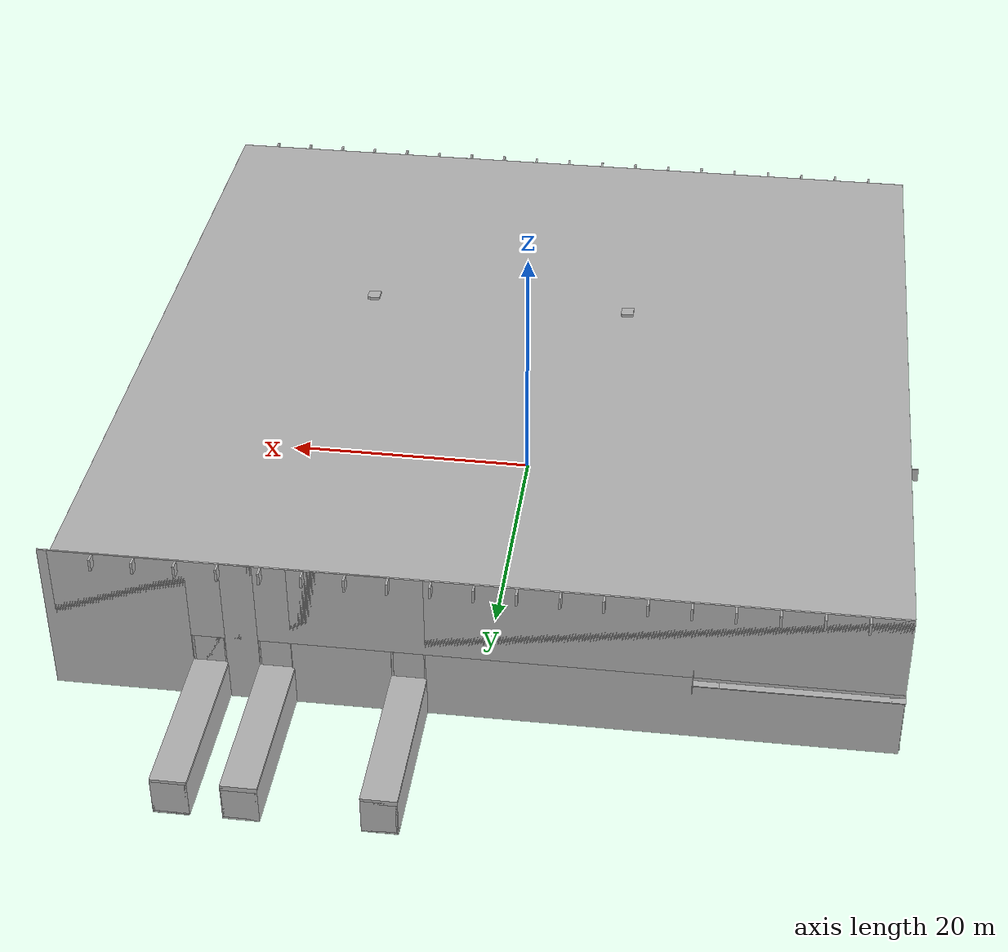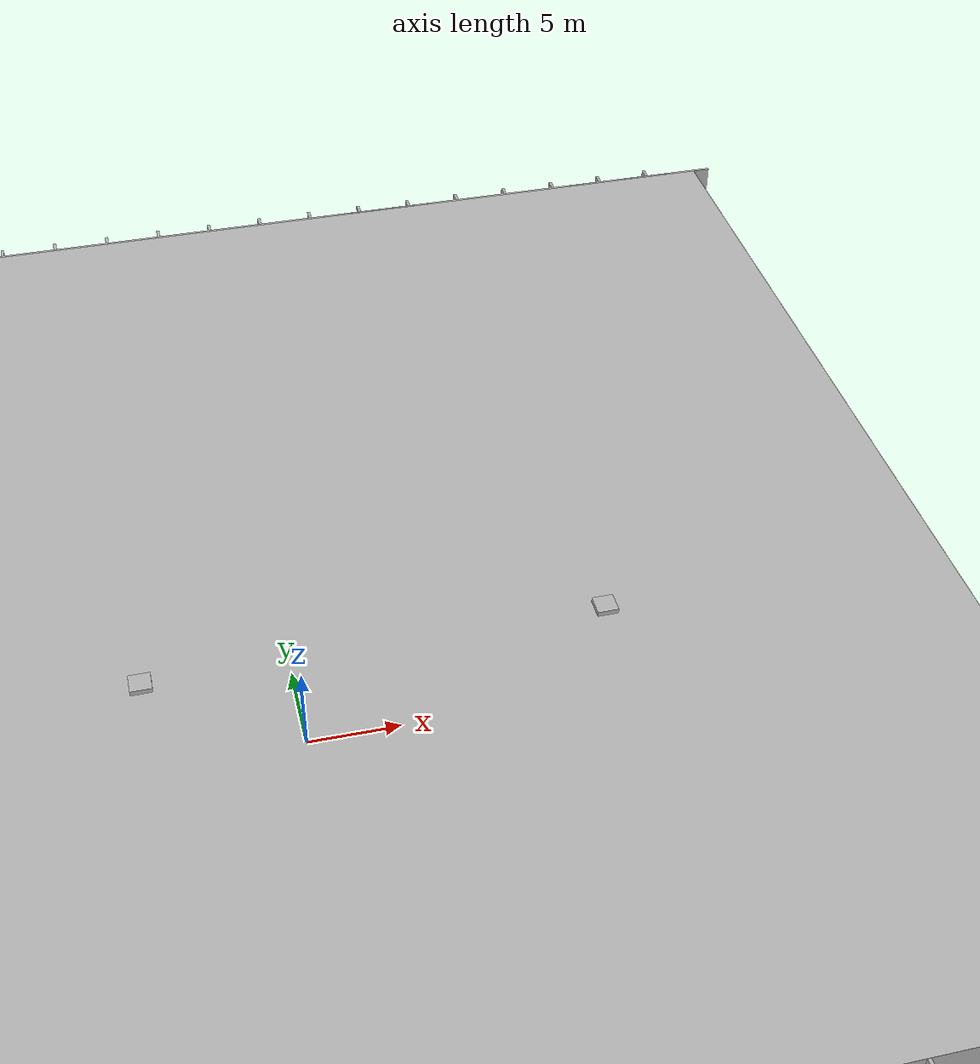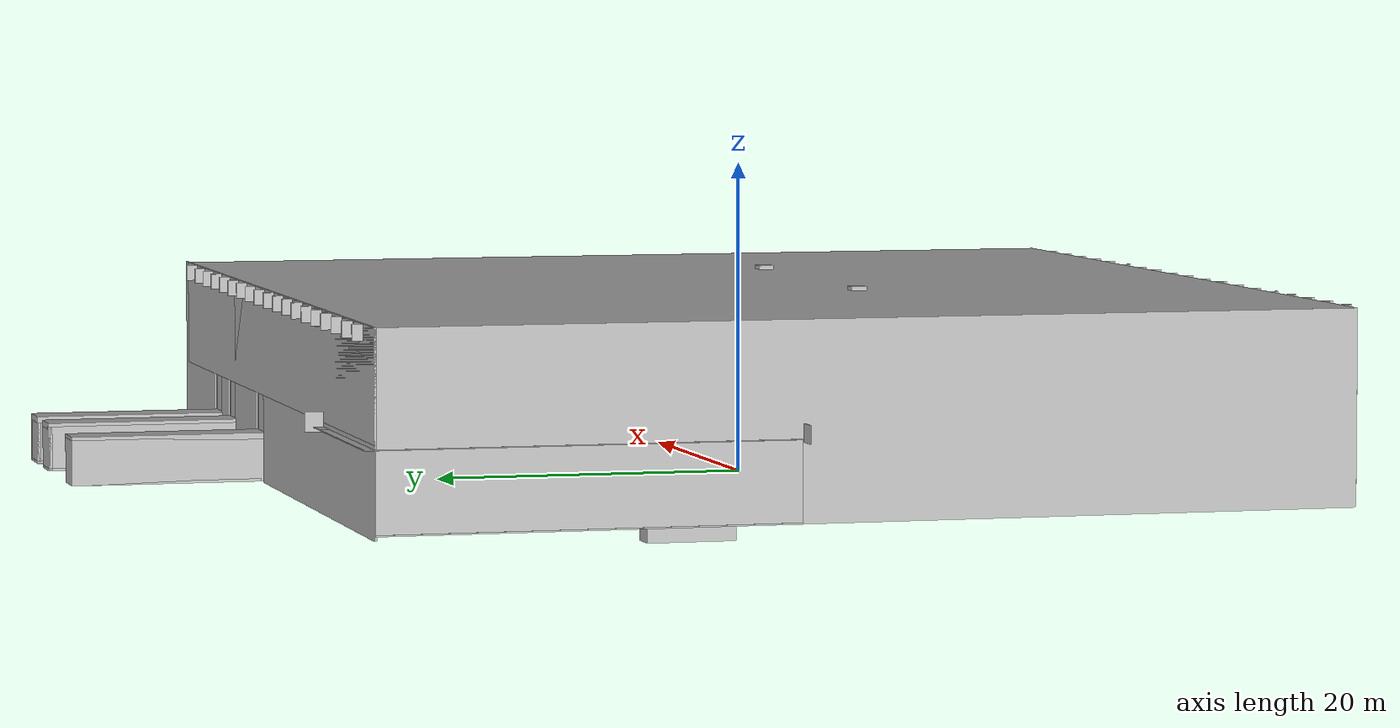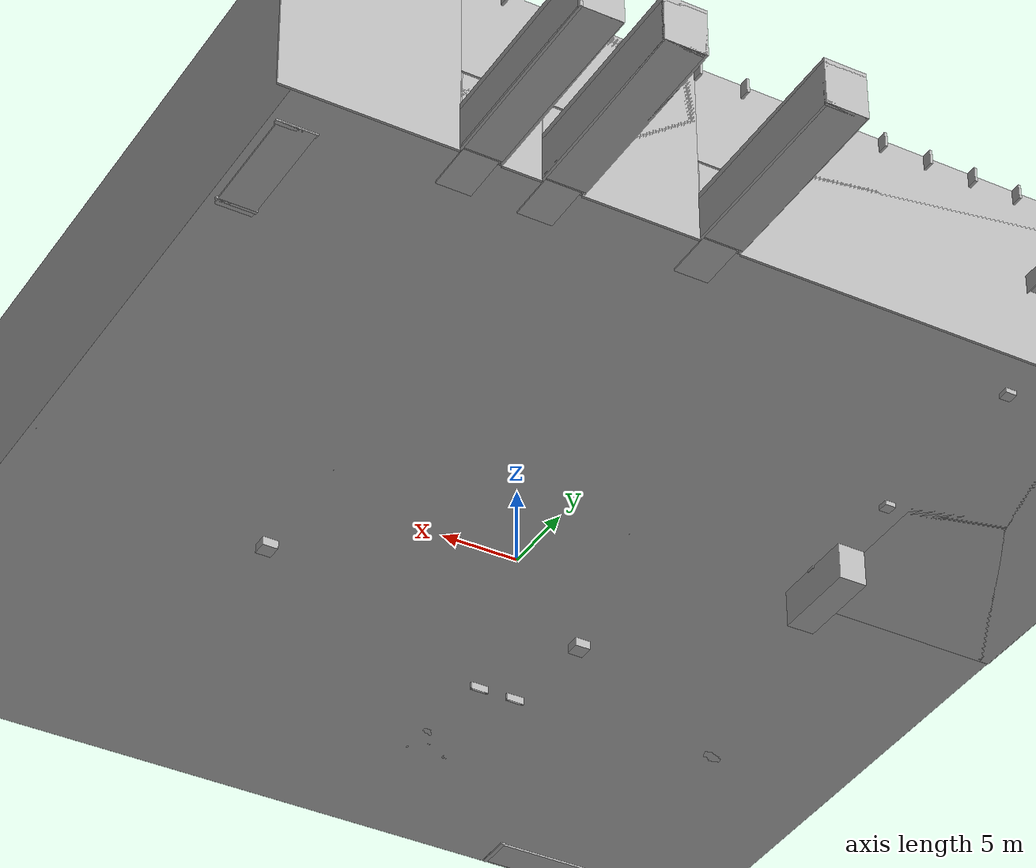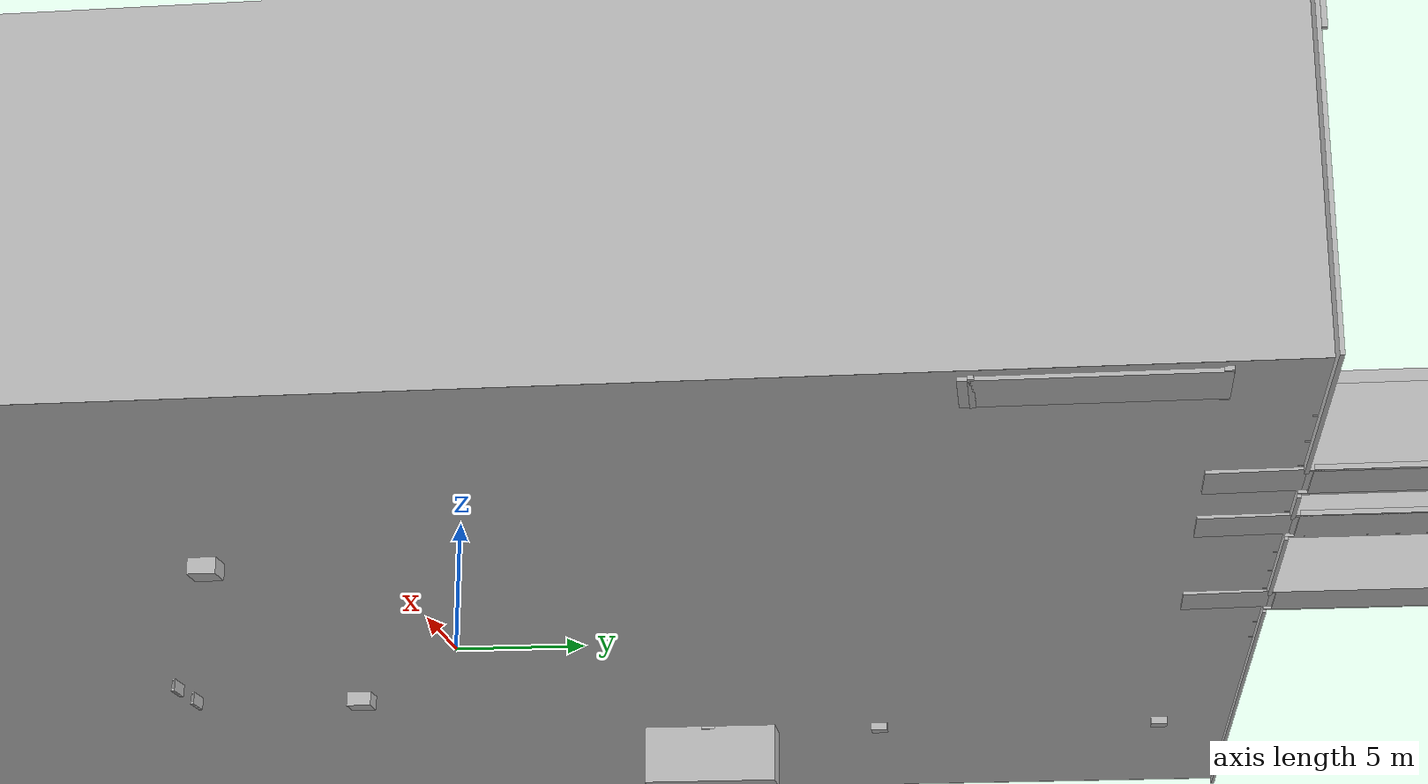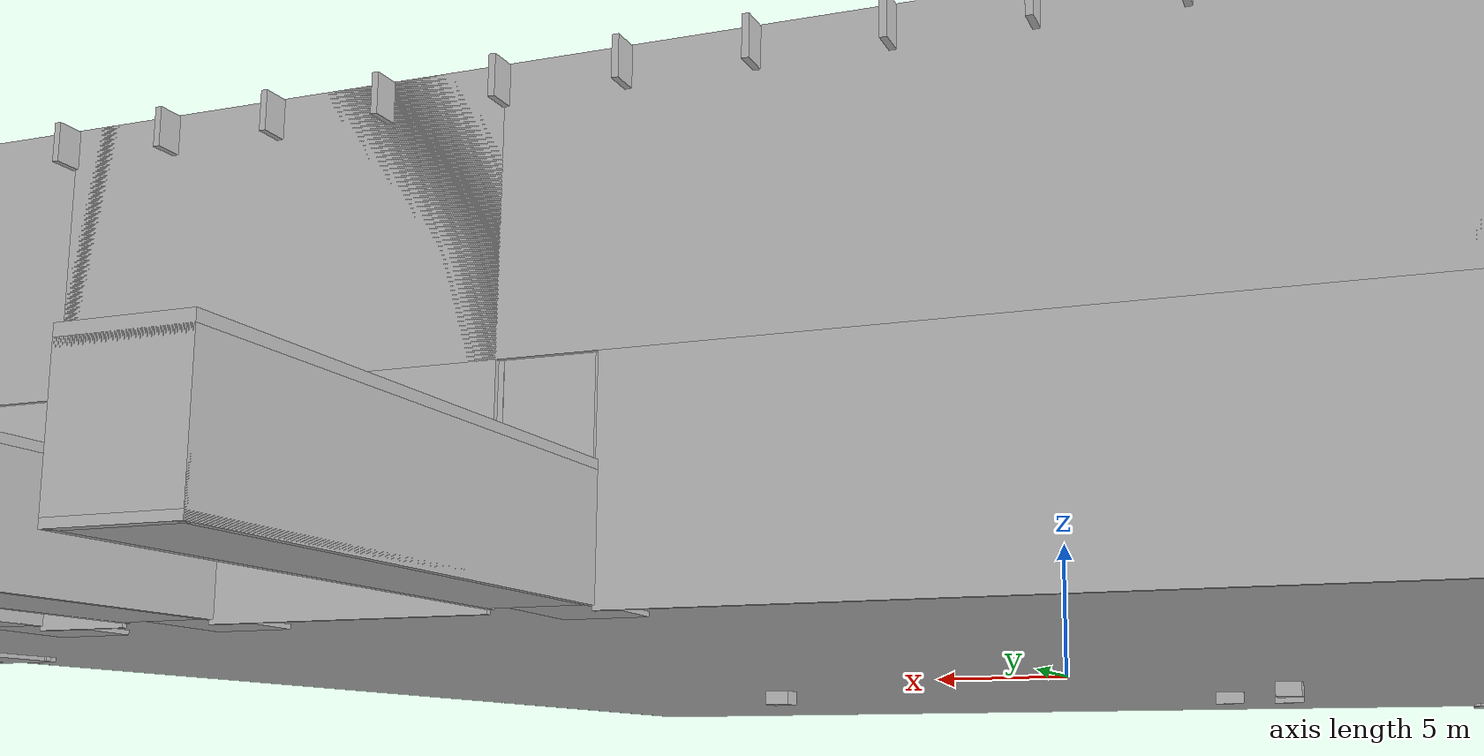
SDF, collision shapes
<?xml version="1.0" encoding="UTF-8"?>
<sdf version="1.12">
  <model name="jetty_world">

    <include>
      <static>true</static>
      <name>Distribution Warehouse</name>
      <uri>https://fuel.gazebosim.org/1.0/OpenRobotics/models/Distribution_Warehouse</uri>
    </include>

    <include>
      <static>true</static>
      <name>Picking_Shelves</name>
      <uri>https://fuel.gazebosim.org/1.0/OpenRobotics/models/Picking_Shelves</uri>
      <pose>-7.2612 0.9492 0.0000 0.0000 -0.0000 1.5708</pose>
    </include>

    <include>
      <static>true</static>
      <name>Picking_Shelves.001</name>
      <uri>https://fuel.gazebosim.org/1.0/OpenRobotics/models/Picking_Shelves</uri>
      <pose>-7.2612 1.9492 0.0000 0.0000 -0.0000 1.5708</pose>
    </include>

    <include>
      <static>true</static>
      <name>Picking_Shelves.002</name>
      <uri>https://fuel.gazebosim.org/1.0/OpenRobotics/models/Picking_Shelves</uri>
      <pose>-7.2612 2.9492 0.0000 0.0000 -0.0000 1.5708</pose>
    </include>

    <include>
      <static>true</static>
      <name>Picking_Shelves.003</name>
      <uri>https://fuel.gazebosim.org/1.0/OpenRobotics/models/Picking_Shelves</uri>
      <pose>-7.2612 3.9492 0.0000 0.0000 -0.0000 1.5708</pose>
    </include>

    <include>
      <static>true</static>
      <name>Picking_Shelves.004</name>
      <uri>https://fuel.gazebosim.org/1.0/OpenRobotics/models/Picking_Shelves</uri>
      <pose>-7.2612 4.9492 0.0000 0.0000 -0.0000 1.5708</pose>
    </include>

    <include>
      <static>true</static>
      <name>Picking_Shelves.005</name>
      <uri>https://fuel.gazebosim.org/1.0/OpenRobotics/models/Picking_Shelves</uri>
      <pose>-7.2612 5.9492 0.0000 0.0000 -0.0000 1.5708</pose>
    </include>

    <include>
      <static>true</static>
      <name>Picking_Shelves.006</name>
      <uri>https://fuel.gazebosim.org/1.0/OpenRobotics/models/Picking_Shelves</uri>
      <pose>-4.2612 -0.0508 0.0000 0.0000 -0.0000 1.5708</pose>
    </include>

    <include>
      <static>true</static>
      <name>Picking_Shelves.007</name>
      <uri>https://fuel.gazebosim.org/1.0/OpenRobotics/models/Picking_Shelves</uri>
      <pose>-4.2612 0.9492 0.0000 0.0000 -0.0000 1.5708</pose>
    </include>

    <include>
      <static>true</static>
      <name>Picking_Shelves.008</name>
      <uri>https://fuel.gazebosim.org/1.0/OpenRobotics/models/Picking_Shelves</uri>
      <pose>-4.2612 1.9492 0.0000 0.0000 -0.0000 1.5708</pose>
    </include>

    <include>
      <static>true</static>
      <name>Picking_Shelves.009</name>
      <uri>https://fuel.gazebosim.org/1.0/OpenRobotics/models/Picking_Shelves</uri>
      <pose>-4.2612 2.9492 0.0000 0.0000 -0.0000 1.5708</pose>
    </include>

    <include>
      <static>true</static>
      <name>Picking_Shelves.010</name>
      <uri>https://fuel.gazebosim.org/1.0/OpenRobotics/models/Picking_Shelves</uri>
      <pose>-4.2612 3.9492 0.0000 0.0000 -0.0000 1.5708</pose>
    </include>

    <include>
      <static>true</static>
      <name>Picking_Shelves.011</name>
      <uri>https://fuel.gazebosim.org/1.0/OpenRobotics/models/Picking_Shelves</uri>
      <pose>-4.2612 4.9492 0.0000 0.0000 -0.0000 1.5708</pose>
    </include>

    <include>
      <static>true</static>
      <name>Picking_Shelves.012</name>
      <uri>https://fuel.gazebosim.org/1.0/OpenRobotics/models/Picking_Shelves</uri>
      <pose>-4.2612 5.9492 0.0000 0.0000 -0.0000 1.5708</pose>
    </include>

    <include>
      <static>true</static>
      <name>Picking_Shelves.013</name>
      <uri>https://fuel.gazebosim.org/1.0/OpenRobotics/models/Picking_Shelves</uri>
      <pose>-3.7612 -0.0508 0.0000 0.0000 -0.0000 1.5708</pose>
    </include>

    <include>
      <static>true</static>
      <name>Picking_Shelves.014</name>
      <uri>https://fuel.gazebosim.org/1.0/OpenRobotics/models/Picking_Shelves</uri>
      <pose>-3.7612 0.9492 0.0000 0.0000 -0.0000 1.5708</pose>
    </include>

    <include>
      <static>true</static>
      <name>Picking_Shelves.015</name>
      <uri>https://fuel.gazebosim.org/1.0/OpenRobotics/models/Picking_Shelves</uri>
      <pose>-3.7612 1.9492 0.0000 0.0000 -0.0000 1.5708</pose>
    </include>

    <include>
      <static>true</static>
      <name>Picking_Shelves.016</name>
      <uri>https://fuel.gazebosim.org/1.0/OpenRobotics/models/Picking_Shelves</uri>
      <pose>-3.7612 2.9492 0.0000 0.0000 -0.0000 1.5708</pose>
    </include>

    <include>
      <static>true</static>
      <name>Picking_Shelves.017</name>
      <uri>https://fuel.gazebosim.org/1.0/OpenRobotics/models/Picking_Shelves</uri>
      <pose>-3.7612 3.9492 0.0000 0.0000 -0.0000 1.5708</pose>
    </include>

    <include>
      <static>true</static>
      <name>Picking_Shelves.018</name>
      <uri>https://fuel.gazebosim.org/1.0/OpenRobotics/models/Picking_Shelves</uri>
      <pose>-3.7612 4.9492 0.0000 0.0000 -0.0000 1.5708</pose>
    </include>

    <include>
      <static>true</static>
      <name>Picking_Shelves.019</name>
      <uri>https://fuel.gazebosim.org/1.0/OpenRobotics/models/Picking_Shelves</uri>
      <pose>-3.7612 5.9492 0.0000 0.0000 -0.0000 1.5708</pose>
    </include>

    <include>
      <static>true</static>
      <name>Picking_Shelves.020</name>
      <uri>https://fuel.gazebosim.org/1.0/OpenRobotics/models/Picking_Shelves</uri>
      <pose>-0.7612 -0.0508 0.0000 0.0000 -0.0000 1.5708</pose>
    </include>

    <include>
      <static>true</static>
      <name>Picking_Shelves.021</name>
      <uri>https://fuel.gazebosim.org/1.0/OpenRobotics/models/Picking_Shelves</uri>
      <pose>-0.7612 0.9492 0.0000 0.0000 -0.0000 1.5708</pose>
    </include>

    <include>
      <static>true</static>
      <name>Picking_Shelves.022</name>
      <uri>https://fuel.gazebosim.org/1.0/OpenRobotics/models/Picking_Shelves</uri>
      <pose>-0.7612 1.9492 0.0000 0.0000 -0.0000 1.5708</pose>
    </include>

    <include>
      <static>true</static>
      <name>Picking_Shelves.023</name>
      <uri>https://fuel.gazebosim.org/1.0/OpenRobotics/models/Picking_Shelves</uri>
      <pose>-0.7612 2.9492 0.0000 0.0000 -0.0000 1.5708</pose>
    </include>

    <include>
      <static>true</static>
      <name>Picking_Shelves.024</name>
      <uri>https://fuel.gazebosim.org/1.0/OpenRobotics/models/Picking_Shelves</uri>
      <pose>-0.7612 3.9492 0.0000 0.0000 -0.0000 1.5708</pose>
    </include>

    <include>
      <static>true</static>
      <name>Picking_Shelves.025</name>
      <uri>https://fuel.gazebosim.org/1.0/OpenRobotics/models/Picking_Shelves</uri>
      <pose>-0.7612 4.9492 0.0000 0.0000 -0.0000 1.5708</pose>
    </include>

    <include>
      <static>true</static>
      <name>Picking_Shelves.026</name>
      <uri>https://fuel.gazebosim.org/1.0/OpenRobotics/models/Picking_Shelves</uri>
      <pose>-0.7612 5.9492 0.0000 0.0000 -0.0000 1.5708</pose>
    </include>

    <include>
      <static>true</static>
      <name>Picking_Shelves.027</name>
      <uri>https://fuel.gazebosim.org/1.0/OpenRobotics/models/Picking_Shelves</uri>
      <pose>-0.2612 -0.0508 0.0000 0.0000 -0.0000 1.5708</pose>
    </include>

    <include>
      <static>true</static>
      <name>Picking_Shelves.028</name>
      <uri>https://fuel.gazebosim.org/1.0/OpenRobotics/models/Picking_Shelves</uri>
      <pose>-0.2612 0.9492 0.0000 0.0000 -0.0000 1.5708</pose>
    </include>

    <include>
      <static>true</static>
      <name>Picking_Shelves.029</name>
      <uri>https://fuel.gazebosim.org/1.0/OpenRobotics/models/Picking_Shelves</uri>
      <pose>-0.2612 1.9492 0.0000 0.0000 -0.0000 1.5708</pose>
    </include>

    <include>
      <static>true</static>
      <name>Picking_Shelves.030</name>
      <uri>https://fuel.gazebosim.org/1.0/OpenRobotics/models/Picking_Shelves</uri>
      <pose>-0.2612 2.9492 0.0000 0.0000 -0.0000 1.5708</pose>
    </include>

    <include>
      <static>true</static>
      <name>Picking_Shelves.031</name>
      <uri>https://fuel.gazebosim.org/1.0/OpenRobotics/models/Picking_Shelves</uri>
      <pose>-0.2612 3.9492 0.0000 0.0000 -0.0000 1.5708</pose>
    </include>

    <include>
      <static>true</static>
      <name>Picking_Shelves.032</name>
      <uri>https://fuel.gazebosim.org/1.0/OpenRobotics/models/Picking_Shelves</uri>
      <pose>-0.2612 4.9492 0.0000 0.0000 -0.0000 1.5708</pose>
    </include>

    <include>
      <static>true</static>
      <name>Picking_Shelves.033</name>
      <uri>https://fuel.gazebosim.org/1.0/OpenRobotics/models/Picking_Shelves</uri>
      <pose>-0.2612 5.9492 0.0000 0.0000 -0.0000 1.5708</pose>
    </include>

    <include>
      <static>true</static>
      <name>Picking_Shelves.034</name>
      <uri>https://fuel.gazebosim.org/1.0/OpenRobotics/models/Picking_Shelves</uri>
      <pose>2.7388 -0.0508 0.0000 0.0000 -0.0000 1.5708</pose>
    </include>

    <include>
      <static>true</static>
      <name>Picking_Shelves.035</name>
      <uri>https://fuel.gazebosim.org/1.0/OpenRobotics/models/Picking_Shelves</uri>
      <pose>2.7388 0.9492 0.0000 0.0000 -0.0000 1.5708</pose>
    </include>

    <include>
      <static>true</static>
      <name>Picking_Shelves.036</name>
      <uri>https://fuel.gazebosim.org/1.0/OpenRobotics/models/Picking_Shelves</uri>
      <pose>2.7388 1.9492 0.0000 0.0000 -0.0000 1.5708</pose>
    </include>

    <include>
      <static>true</static>
      <name>Picking_Shelves.037</name>
      <uri>https://fuel.gazebosim.org/1.0/OpenRobotics/models/Picking_Shelves</uri>
      <pose>2.7388 2.9492 0.0000 0.0000 -0.0000 1.5708</pose>
    </include>

    <include>
      <static>true</static>
      <name>Picking_Shelves.038</name>
      <uri>https://fuel.gazebosim.org/1.0/OpenRobotics/models/Picking_Shelves</uri>
      <pose>-7.2612 -0.0508 0.0000 0.0000 -0.0000 1.5708</pose>
    </include>

    <include>
      <static>true</static>
      <name>Picking_Shelves.039</name>
      <uri>https://fuel.gazebosim.org/1.0/OpenRobotics/models/Picking_Shelves</uri>
      <pose>2.7388 3.9492 0.0000 0.0000 -0.0000 1.5708</pose>
    </include>

    <include>
      <static>true</static>
      <name>Picking_Shelves.040</name>
      <uri>https://fuel.gazebosim.org/1.0/OpenRobotics/models/Picking_Shelves</uri>
      <pose>2.7388 4.9492 0.0000 0.0000 -0.0000 1.5708</pose>
    </include>

    <include>
      <static>true</static>
      <name>Picking_Shelves.041</name>
      <uri>https://fuel.gazebosim.org/1.0/OpenRobotics/models/Picking_Shelves</uri>
      <pose>2.7388 5.9492 0.0000 0.0000 -0.0000 1.5708</pose>
    </include>

    <include>
      <static>true</static>
      <name>Picking_Shelves.042</name>
      <uri>https://fuel.gazebosim.org/1.0/OpenRobotics/models/Picking_Shelves</uri>
      <pose>3.2388 -0.0508 0.0000 0.0000 -0.0000 1.5708</pose>
    </include>

    <include>
      <static>true</static>
      <name>Picking_Shelves.043</name>
      <uri>https://fuel.gazebosim.org/1.0/OpenRobotics/models/Picking_Shelves</uri>
      <pose>3.2388 0.9492 0.0000 0.0000 -0.0000 1.5708</pose>
    </include>

    <include>
      <static>true</static>
      <name>Picking_Shelves.044</name>
      <uri>https://fuel.gazebosim.org/1.0/OpenRobotics/models/Picking_Shelves</uri>
      <pose>3.2388 1.9492 0.0000 0.0000 -0.0000 1.5708</pose>
    </include>

    <include>
      <static>true</static>
      <name>Picking_Shelves.045</name>
      <uri>https://fuel.gazebosim.org/1.0/OpenRobotics/models/Picking_Shelves</uri>
      <pose>3.2388 2.9492 0.0000 0.0000 -0.0000 1.5708</pose>
    </include>

    <include>
      <static>true</static>
      <name>Picking_Shelves.046</name>
      <uri>https://fuel.gazebosim.org/1.0/OpenRobotics/models/Picking_Shelves</uri>
      <pose>3.2388 3.9492 0.0000 0.0000 -0.0000 1.5708</pose>
    </include>

    <include>
      <static>true</static>
      <name>Picking_Shelves.047</name>
      <uri>https://fuel.gazebosim.org/1.0/OpenRobotics/models/Picking_Shelves</uri>
      <pose>3.2388 4.9492 0.0000 0.0000 -0.0000 1.5708</pose>
    </include>

    <include>
      <static>true</static>
      <name>Picking_Shelves.048</name>
      <uri>https://fuel.gazebosim.org/1.0/OpenRobotics/models/Picking_Shelves</uri>
      <pose>3.2388 5.9492 0.0000 0.0000 -0.0000 1.5708</pose>
    </include>

    <include>
      <static>true</static>
      <name>Picking_Shelves.049</name>
      <uri>https://fuel.gazebosim.org/1.0/OpenRobotics/models/Picking_Shelves</uri>
      <pose>6.2388 -0.0508 0.0000 0.0000 -0.0000 1.5708</pose>
    </include>

    <include>
      <static>true</static>
      <name>Picking_Shelves.050</name>
      <uri>https://fuel.gazebosim.org/1.0/OpenRobotics/models/Picking_Shelves</uri>
      <pose>6.2388 0.9492 0.0000 0.0000 -0.0000 1.5708</pose>
    </include>

    <include>
      <static>true</static>
      <name>Picking_Shelves.051</name>
      <uri>https://fuel.gazebosim.org/1.0/OpenRobotics/models/Picking_Shelves</uri>
      <pose>6.2388 1.9492 0.0000 0.0000 -0.0000 1.5708</pose>
    </include>

    <include>
      <static>true</static>
      <name>Picking_Shelves.052</name>
      <uri>https://fuel.gazebosim.org/1.0/OpenRobotics/models/Picking_Shelves</uri>
      <pose>6.2388 2.9492 0.0000 0.0000 -0.0000 1.5708</pose>
    </include>

    <include>
      <static>true</static>
      <name>Picking_Shelves.053</name>
      <uri>https://fuel.gazebosim.org/1.0/OpenRobotics/models/Picking_Shelves</uri>
      <pose>6.2388 3.9492 0.0000 0.0000 -0.0000 1.5708</pose>
    </include>

    <include>
      <static>true</static>
      <name>Picking_Shelves.054</name>
      <uri>https://fuel.gazebosim.org/1.0/OpenRobotics/models/Picking_Shelves</uri>
      <pose>6.2388 4.9492 0.0000 0.0000 -0.0000 1.5708</pose>
    </include>

    <include>
      <static>true</static>
      <name>Picking_Shelves.055</name>
      <uri>https://fuel.gazebosim.org/1.0/OpenRobotics/models/Picking_Shelves</uri>
      <pose>6.2388 5.9492 0.0000 0.0000 -0.0000 1.5708</pose>
    </include>

    <include>
      <static>true</static>
      <name>Picking_Shelves.056</name>
      <uri>https://fuel.gazebosim.org/1.0/OpenRobotics/models/Picking_Shelves</uri>
      <pose>6.7388 -0.0508 0.0000 0.0000 -0.0000 1.5708</pose>
    </include>

    <include>
      <static>true</static>
      <name>Picking_Shelves.057</name>
      <uri>https://fuel.gazebosim.org/1.0/OpenRobotics/models/Picking_Shelves</uri>
      <pose>6.7388 0.9492 0.0000 0.0000 -0.0000 1.5708</pose>
    </include>

    <include>
      <static>true</static>
      <name>Picking_Shelves.058</name>
      <uri>https://fuel.gazebosim.org/1.0/OpenRobotics/models/Picking_Shelves</uri>
      <pose>6.7388 1.9492 0.0000 0.0000 -0.0000 1.5708</pose>
    </include>

    <include>
      <static>true</static>
      <name>Picking_Shelves.059</name>
      <uri>https://fuel.gazebosim.org/1.0/OpenRobotics/models/Picking_Shelves</uri>
      <pose>6.7388 2.9492 0.0000 0.0000 -0.0000 1.5708</pose>
    </include>

    <include>
      <static>true</static>
      <name>Picking_Shelves.060</name>
      <uri>https://fuel.gazebosim.org/1.0/OpenRobotics/models/Picking_Shelves</uri>
      <pose>6.7388 3.9492 0.0000 0.0000 -0.0000 1.5708</pose>
    </include>

    <include>
      <static>true</static>
      <name>Picking_Shelves.061</name>
      <uri>https://fuel.gazebosim.org/1.0/OpenRobotics/models/Picking_Shelves</uri>
      <pose>6.7388 4.9492 0.0000 0.0000 -0.0000 1.5708</pose>
    </include>

    <include>
      <static>true</static>
      <name>Picking_Shelves.062</name>
      <uri>https://fuel.gazebosim.org/1.0/OpenRobotics/models/Picking_Shelves</uri>
      <pose>6.7388 5.9492 0.0000 0.0000 -0.0000 1.5708</pose>
    </include>

    <include>
      <static>true</static>
      <name>Picking_Shelves.063</name>
      <uri>https://fuel.gazebosim.org/1.0/OpenRobotics/models/Picking_Shelves</uri>
      <pose>9.7388 -0.0508 0.0000 0.0000 -0.0000 1.5708</pose>
    </include>

    <include>
      <static>true</static>
      <name>Picking_Shelves.064</name>
      <uri>https://fuel.gazebosim.org/1.0/OpenRobotics/models/Picking_Shelves</uri>
      <pose>9.7388 0.9492 0.0000 0.0000 -0.0000 1.5708</pose>
    </include>

    <include>
      <static>true</static>
      <name>Picking_Shelves.065</name>
      <uri>https://fuel.gazebosim.org/1.0/OpenRobotics/models/Picking_Shelves</uri>
      <pose>9.7388 1.9492 0.0000 0.0000 -0.0000 1.5708</pose>
    </include>

    <include>
      <static>true</static>
      <name>Picking_Shelves.066</name>
      <uri>https://fuel.gazebosim.org/1.0/OpenRobotics/models/Picking_Shelves</uri>
      <pose>9.7388 2.9492 0.0000 0.0000 -0.0000 1.5708</pose>
    </include>

    <include>
      <static>true</static>
      <name>Picking_Shelves.067</name>
      <uri>https://fuel.gazebosim.org/1.0/OpenRobotics/models/Picking_Shelves</uri>
      <pose>9.7388 3.9492 0.0000 0.0000 -0.0000 1.5708</pose>
    </include>

    <include>
      <static>true</static>
      <name>Picking_Shelves.068</name>
      <uri>https://fuel.gazebosim.org/1.0/OpenRobotics/models/Picking_Shelves</uri>
      <pose>9.7388 4.9492 0.0000 0.0000 -0.0000 1.5708</pose>
    </include>

    <include>
      <static>true</static>
      <name>Picking_Shelves.069</name>
      <uri>https://fuel.gazebosim.org/1.0/OpenRobotics/models/Picking_Shelves</uri>
      <pose>9.7388 5.9492 0.0000 0.0000 -0.0000 1.5708</pose>
    </include>

    <include>
      <static>true</static>
      <name>Picking_Shelves.070</name>
      <uri>https://fuel.gazebosim.org/1.0/OpenRobotics/models/Picking_Shelves</uri>
      <pose>10.2388 -0.0508 0.0000 0.0000 -0.0000 1.5708</pose>
    </include>

    <include>
      <static>true</static>
      <name>Picking_Shelves.071</name>
      <uri>https://fuel.gazebosim.org/1.0/OpenRobotics/models/Picking_Shelves</uri>
      <pose>10.2388 0.9492 0.0000 0.0000 -0.0000 1.5708</pose>
    </include>

    <include>
      <static>true</static>
      <name>Picking_Shelves.072</name>
      <uri>https://fuel.gazebosim.org/1.0/OpenRobotics/models/Picking_Shelves</uri>
      <pose>10.2388 1.9492 0.0000 0.0000 -0.0000 1.5708</pose>
    </include>

    <include>
      <static>true</static>
      <name>Picking_Shelves.073</name>
      <uri>https://fuel.gazebosim.org/1.0/OpenRobotics/models/Picking_Shelves</uri>
      <pose>10.2388 2.9492 0.0000 0.0000 -0.0000 1.5708</pose>
    </include>

    <include>
      <static>true</static>
      <name>Picking_Shelves.074</name>
      <uri>https://fuel.gazebosim.org/1.0/OpenRobotics/models/Picking_Shelves</uri>
      <pose>10.2388 3.9492 0.0000 0.0000 -0.0000 1.5708</pose>
    </include>

    <include>
      <static>true</static>
      <name>Picking_Shelves.075</name>
      <uri>https://fuel.gazebosim.org/1.0/OpenRobotics/models/Picking_Shelves</uri>
      <pose>10.2388 4.9492 0.0000 0.0000 -0.0000 1.5708</pose>
    </include>

    <include>
      <static>true</static>
      <name>Picking_Shelves.076</name>
      <uri>https://fuel.gazebosim.org/1.0/OpenRobotics/models/Picking_Shelves</uri>
      <pose>10.2388 5.9492 0.0000 0.0000 -0.0000 1.5708</pose>
    </include>

    <include>
      <static>true</static>
      <name>Picking_Shelves.077</name>
      <uri>https://fuel.gazebosim.org/1.0/OpenRobotics/models/Picking_Shelves</uri>
      <pose>13.2388 -0.0508 0.0000 0.0000 -0.0000 1.5708</pose>
    </include>

    <include>
      <static>true</static>
      <name>Picking_Shelves.078</name>
      <uri>https://fuel.gazebosim.org/1.0/OpenRobotics/models/Picking_Shelves</uri>
      <pose>13.2388 0.9492 0.0000 0.0000 -0.0000 1.5708</pose>
    </include>

    <include>
      <static>true</static>
      <name>Picking_Shelves.079</name>
      <uri>https://fuel.gazebosim.org/1.0/OpenRobotics/models/Picking_Shelves</uri>
      <pose>13.2388 1.9492 0.0000 0.0000 -0.0000 1.5708</pose>
    </include>

    <include>
      <static>true</static>
      <name>Picking_Shelves.080</name>
      <uri>https://fuel.gazebosim.org/1.0/OpenRobotics/models/Picking_Shelves</uri>
      <pose>13.2388 2.9492 0.0000 0.0000 -0.0000 1.5708</pose>
    </include>

    <include>
      <static>true</static>
      <name>Picking_Shelves.081</name>
      <uri>https://fuel.gazebosim.org/1.0/OpenRobotics/models/Picking_Shelves</uri>
      <pose>13.2388 3.9492 0.0000 0.0000 -0.0000 1.5708</pose>
    </include>

    <include>
      <static>true</static>
      <name>Picking_Shelves.082</name>
      <uri>https://fuel.gazebosim.org/1.0/OpenRobotics/models/Picking_Shelves</uri>
      <pose>13.2388 4.9492 0.0000 0.0000 -0.0000 1.5708</pose>
    </include>

    <include>
      <static>true</static>
      <name>Picking_Shelves.083</name>
      <uri>https://fuel.gazebosim.org/1.0/OpenRobotics/models/Picking_Shelves</uri>
      <pose>13.2388 5.9492 0.0000 0.0000 -0.0000 1.5708</pose>
    </include>

    <include>
      <static>true</static>
      <name>Picking_Shelves.084</name>
      <uri>https://fuel.gazebosim.org/1.0/OpenRobotics/models/Picking_Shelves</uri>
      <pose>13.7388 -0.0508 0.0000 0.0000 -0.0000 1.5708</pose>
    </include>

    <include>
      <static>true</static>
      <name>Picking_Shelves.085</name>
      <uri>https://fuel.gazebosim.org/1.0/OpenRobotics/models/Picking_Shelves</uri>
      <pose>13.7388 0.9492 0.0000 0.0000 -0.0000 1.5708</pose>
    </include>

    <include>
      <static>true</static>
      <name>Picking_Shelves.086</name>
      <uri>https://fuel.gazebosim.org/1.0/OpenRobotics/models/Picking_Shelves</uri>
      <pose>13.7388 1.9492 0.0000 0.0000 -0.0000 1.5708</pose>
    </include>

    <include>
      <static>true</static>
      <name>Picking_Shelves.087</name>
      <uri>https://fuel.gazebosim.org/1.0/OpenRobotics/models/Picking_Shelves</uri>
      <pose>13.7388 2.9492 0.0000 0.0000 -0.0000 1.5708</pose>
    </include>

    <include>
      <static>true</static>
      <name>Picking_Shelves.088</name>
      <uri>https://fuel.gazebosim.org/1.0/OpenRobotics/models/Picking_Shelves</uri>
      <pose>13.7388 3.9492 0.0000 0.0000 -0.0000 1.5708</pose>
    </include>

    <include>
      <static>true</static>
      <name>Picking_Shelves.089</name>
      <uri>https://fuel.gazebosim.org/1.0/OpenRobotics/models/Picking_Shelves</uri>
      <pose>13.7388 4.9492 0.0000 0.0000 -0.0000 1.5708</pose>
    </include>

    <include>
      <static>true</static>
      <name>Picking_Shelves.090</name>
      <uri>https://fuel.gazebosim.org/1.0/OpenRobotics/models/Picking_Shelves</uri>
      <pose>13.7388 5.9492 0.0000 0.0000 -0.0000 1.5708</pose>
    </include>

    <include>
      <static>true</static>
      <name>Picking_Shelves.091</name>
      <uri>https://fuel.gazebosim.org/1.0/OpenRobotics/models/Picking_Shelves</uri>
      <pose>16.7388 -0.0508 0.0000 0.0000 -0.0000 1.5708</pose>
    </include>

    <include>
      <static>true</static>
      <name>Picking_Shelves.092</name>
      <uri>https://fuel.gazebosim.org/1.0/OpenRobotics/models/Picking_Shelves</uri>
      <pose>16.7388 0.9492 0.0000 0.0000 -0.0000 1.5708</pose>
    </include>

    <include>
      <static>true</static>
      <name>Picking_Shelves.093</name>
      <uri>https://fuel.gazebosim.org/1.0/OpenRobotics/models/Picking_Shelves</uri>
      <pose>16.7388 1.9492 0.0000 0.0000 -0.0000 1.5708</pose>
    </include>

    <include>
      <static>true</static>
      <name>Picking_Shelves.094</name>
      <uri>https://fuel.gazebosim.org/1.0/OpenRobotics/models/Picking_Shelves</uri>
      <pose>16.7388 2.9492 0.0000 0.0000 -0.0000 1.5708</pose>
    </include>

    <include>
      <static>true</static>
      <name>Picking_Shelves.095</name>
      <uri>https://fuel.gazebosim.org/1.0/OpenRobotics/models/Picking_Shelves</uri>
      <pose>16.7388 3.9492 0.0000 0.0000 -0.0000 1.5708</pose>
    </include>

    <include>
      <static>true</static>
      <name>Picking_Shelves.096</name>
      <uri>https://fuel.gazebosim.org/1.0/OpenRobotics/models/Picking_Shelves</uri>
      <pose>16.7388 4.9492 0.0000 0.0000 -0.0000 1.5708</pose>
    </include>

    <include>
      <static>true</static>
      <name>Picking_Shelves.097</name>
      <uri>https://fuel.gazebosim.org/1.0/OpenRobotics/models/Picking_Shelves</uri>
      <pose>16.7388 5.9492 0.0000 0.0000 -0.0000 1.5708</pose>
    </include>

    <include>
      <static>true</static>
      <name>55gal_Drum</name>
      <uri>https://fuel.gazebosim.org/1.0/OpenRobotics/models/55gal_Drum</uri>
      <pose>30.0657 -3.3757 0.0000 0.0000 -0.0000 0.0000</pose>
    </include>

    <include>
      <static>true</static>
      <name>55gal_Drum.001</name>
      <uri>https://fuel.gazebosim.org/1.0/OpenRobotics/models/55gal_Drum</uri>
      <pose>30.0657 -2.5122 0.0000 0.0000 -0.0000 0.0000</pose>
    </include>

    <include>
      <static>true</static>
      <name>55gal_Drum.002</name>
      <uri>https://fuel.gazebosim.org/1.0/OpenRobotics/models/55gal_Drum</uri>
      <pose>30.0337 -1.7386 0.0000 0.0000 -0.0000 0.0000</pose>
    </include>

    <include>
      <static>true</static>
      <name>55gal_Drum.003</name>
      <uri>https://fuel.gazebosim.org/1.0/OpenRobotics/models/55gal_Drum</uri>
      <pose>29.3741 -2.2211 0.0000 0.0000 -0.0000 0.0000</pose>
    </include>

    <include>
      <static>true</static>
      <name>55gal_Drum.004</name>
      <uri>https://fuel.gazebosim.org/1.0/OpenRobotics/models/55gal_Drum</uri>
      <pose>29.4938 -3.0603 0.0000 0.0000 -0.0000 0.0000</pose>
    </include>

    <include>
      <static>true</static>
      <name>Cable_Spool</name>
      <uri>https://fuel.gazebosim.org/1.0/OpenRobotics/models/Cable_Spool</uri>
      <pose>29.9051 -9.0959 0.0000 0.0000 -0.0000 0.0000</pose>
    </include>

    <include>
      <static>true</static>
      <name>Cable_Spool.001</name>
      <uri>https://fuel.gazebosim.org/1.0/OpenRobotics/models/Cable_Spool</uri>
      <pose>29.7221 -10.2336 0.4916 -1.5708 -0.0000 -0.4013</pose>
    </include>

    <include>
      <static>true</static>
      <name>Cable_Spool.002</name>
      <uri>https://fuel.gazebosim.org/1.0/OpenRobotics/models/Cable_Spool</uri>
      <pose>29.3782 -10.6325 0.0000 0.0000 -0.0000 0.0000</pose>
    </include>

    <include>
      <static>true</static>
      <name>Cable_Spool.003</name>
      <uri>https://fuel.gazebosim.org/1.0/OpenRobotics/models/Cable_Spool</uri>
      <pose>30.4837 -10.9715 0.4916 -1.5708 -0.0000 1.5708</pose>
    </include>

    <include>
      <static>true</static>
      <name>Dumpster_Large</name>
      <uri>https://fuel.gazebosim.org/1.0/OpenRobotics/models/Dumpster_Large</uri>
      <pose>28.8856 24.1307 0.0000 0.0000 -0.0000 1.5708</pose>
    </include>

    <include>
      <static>true</static>
      <name>Dumpster_Large.001</name>
      <uri>https://fuel.gazebosim.org/1.0/OpenRobotics/models/Dumpster_Large</uri>
      <pose>-18.4293 -29.0935 0.0000 0.0000 -0.0000 0.0000</pose>
    </include>

    <include>
      <static>true</static>
      <name>Hand_Cart.001</name>
      <uri>https://fuel.gazebosim.org/1.0/OpenRobotics/models/Hand_Cart</uri>
      <pose>23.6445 -29.0120 0.0000 0.0000 0.0000 -1.5957</pose>
    </include>

    <include>
      <static>true</static>
      <name>Hand_Cart.002</name>
      <uri>https://fuel.gazebosim.org/1.0/OpenRobotics/models/Hand_Cart</uri>
      <pose>19.8893 -28.7736 0.0000 0.0000 0.0000 -1.7779</pose>
    </include>

    <include>
      <static>true</static>
      <name>Hand_Cart.003</name>
      <uri>https://fuel.gazebosim.org/1.0/OpenRobotics/models/Hand_Cart</uri>
      <pose>-10.2822 -0.8198 0.0000 0.0000 -0.0000 0.4128</pose>
    </include>

    <include>
      <static>true</static>
      <name>Packing_Station</name>
      <uri>https://fuel.gazebosim.org/1.0/OpenRobotics/models/Packing_Station</uri>
      <pose>0.9342 13.0841 0.0000 0.0000 -0.0000 0.0000</pose>
    </include>

    <include>
      <static>true</static>
      <name>Packing_Station.001</name>
      <uri>https://fuel.gazebosim.org/1.0/OpenRobotics/models/Packing_Station</uri>
      <pose>-4.0658 13.0841 0.0000 0.0000 -0.0000 0.0000</pose>
    </include>

    <include>
      <static>true</static>
      <name>Packing_Station.002</name>
      <uri>https://fuel.gazebosim.org/1.0/OpenRobotics/models/Packing_Station</uri>
      <pose>-0.0912 13.0841 0.0000 0.0000 0.0000 -3.1416</pose>
    </include>

    <include>
      <static>true</static>
      <name>Packing_Station.003</name>
      <uri>https://fuel.gazebosim.org/1.0/OpenRobotics/models/Packing_Station</uri>
      <pose>5.9342 13.0841 0.0000 0.0000 -0.0000 0.0000</pose>
    </include>

    <include>
      <static>true</static>
      <name>Packing_Station.004</name>
      <uri>https://fuel.gazebosim.org/1.0/OpenRobotics/models/Packing_Station</uri>
      <pose>4.9088 13.0841 0.0000 0.0000 0.0000 -3.1416</pose>
    </include>

    <include>
      <static>true</static>
      <name>Packing_Station.005</name>
      <uri>https://fuel.gazebosim.org/1.0/OpenRobotics/models/Packing_Station</uri>
      <pose>10.9342 13.0841 0.0000 0.0000 -0.0000 0.0000</pose>
    </include>

    <include>
      <static>true</static>
      <name>Packing_Station.006</name>
      <uri>https://fuel.gazebosim.org/1.0/OpenRobotics/models/Packing_Station</uri>
      <pose>9.9088 13.0841 0.0000 0.0000 0.0000 -3.1416</pose>
    </include>

    <include>
      <static>true</static>
      <name>Packing_Station.007</name>
      <uri>https://fuel.gazebosim.org/1.0/OpenRobotics/models/Packing_Station</uri>
      <pose>15.9342 13.0841 0.0000 0.0000 -0.0000 0.0000</pose>
    </include>

    <include>
      <static>true</static>
      <name>Packing_Station.008</name>
      <uri>https://fuel.gazebosim.org/1.0/OpenRobotics/models/Packing_Station</uri>
      <pose>14.9088 13.0841 0.0000 0.0000 0.0000 -3.1416</pose>
    </include>

    <include>
      <static>true</static>
      <name>Packing_Station.009</name>
      <uri>https://fuel.gazebosim.org/1.0/OpenRobotics/models/Packing_Station</uri>
      <pose>19.9088 13.0841 0.0000 0.0000 0.0000 -3.1416</pose>
    </include>

    <include>
      <static>true</static>
      <name>Pallet_Standard</name>
      <uri>https://fuel.gazebosim.org/1.0/OpenRobotics/models/Pallet_Standard</uri>
      <pose>16.3462 18.8209 0.0000 0.0000 -0.0000 1.3997</pose>
    </include>

    <include>
      <static>true</static>
      <name>Pallet_Standard.001</name>
      <uri>https://fuel.gazebosim.org/1.0/OpenRobotics/models/Pallet_Standard</uri>
      <pose>-21.2859 -12.4455 0.0000 0.0000 0.0000 -0.2909</pose>
    </include>

    <include>
      <static>true</static>
      <name>Pallet_Standard.002</name>
      <uri>https://fuel.gazebosim.org/1.0/OpenRobotics/models/Pallet_Standard</uri>
      <pose>19.7470 15.4418 0.0000 0.0000 -0.0000 1.3997</pose>
    </include>

    <include>
      <static>true</static>
      <name>Pallet_Standard.003</name>
      <uri>https://fuel.gazebosim.org/1.0/OpenRobotics/models/Pallet_Standard</uri>
      <pose>19.7470 15.4570 0.1448 0.0000 -0.0000 1.4629</pose>
    </include>

    <include>
      <static>true</static>
      <name>Pallet_Standard.004</name>
      <uri>https://fuel.gazebosim.org/1.0/OpenRobotics/models/Pallet_Standard</uri>
      <pose>19.7470 15.3753 0.2894 0.0000 -0.0000 1.3734</pose>
    </include>

    <include>
      <static>true</static>
      <name>Pallet_Standard.006</name>
      <uri>https://fuel.gazebosim.org/1.0/OpenRobotics/models/Pallet_Standard</uri>
      <pose>-4.4823 -7.7842 0.0000 0.0000 -0.0000 0.0000</pose>
    </include>

    <include>
      <static>true</static>
      <name>Pallet_Standard.007</name>
      <uri>https://fuel.gazebosim.org/1.0/OpenRobotics/models/Pallet_Standard</uri>
      <pose>-7.0000 -12.6278 0.0000 -1.5708 0.0000 0.0000</pose>
    </include>

    <include>
      <static>true</static>
      <name>Pallet_Standard.008</name>
      <uri>https://fuel.gazebosim.org/1.0/OpenRobotics/models/Pallet_Standard</uri>
      <pose>-4.4823 -12.6278 0.0000 -1.5708 0.0000 0.0000</pose>
    </include>

    <include>
      <static>true</static>
      <name>Pallet_Standard.009</name>
      <uri>https://fuel.gazebosim.org/1.0/OpenRobotics/models/Pallet_Standard</uri>
      <pose>-7.0000 -14.1208 0.0000 0.0000 0.0000 0.0000</pose>
    </include>

    <include>
      <static>true</static>
      <name>Pallet_Standard.010</name>
      <uri>https://fuel.gazebosim.org/1.0/OpenRobotics/models/Pallet_Standard</uri>
      <pose>-4.4823 -14.1208 0.0000 0.0000 -0.0000 0.0000</pose>
    </include>

    <include>
      <static>true</static>
      <name>Pallet_Standard.011</name>
      <uri>https://fuel.gazebosim.org/1.0/OpenRobotics/models/Pallet_Standard</uri>
      <pose>-7.0000 -18.9644 0.0000 0.0000 -0.0000 0.0000</pose>
    </include>

    <include>
      <static>true</static>
      <name>Pallet_Standard.012</name>
      <uri>https://fuel.gazebosim.org/1.0/OpenRobotics/models/Pallet_Standard</uri>
      <pose>-4.4823 -18.9644 0.0000 0.0000 -0.0000 0.0000</pose>
    </include>

    <include>
      <static>true</static>
      <name>Pallet_Standard.013</name>
      <uri>https://fuel.gazebosim.org/1.0/OpenRobotics/models/Pallet_Standard</uri>
      <pose>-7.0000 -20.4317 0.0000 0.0000 0.0000 0.0000</pose>
    </include>

    <include>
      <static>true</static>
      <name>Pallet_Standard.014</name>
      <uri>https://fuel.gazebosim.org/1.0/OpenRobotics/models/Pallet_Standard</uri>
      <pose>-4.4823 -20.4317 0.0000 0.0000 -0.0000 0.0000</pose>
    </include>

    <include>
      <static>true</static>
      <name>Pallet_Standard.015</name>
      <uri>https://fuel.gazebosim.org/1.0/OpenRobotics/models/Pallet_Standard</uri>
      <pose>-7.0000 -25.2753 0.0000 0.0000 -0.0000 0.0000</pose>
    </include>

    <include>
      <static>true</static>
      <name>Pallet_Standard.016</name>
      <uri>https://fuel.gazebosim.org/1.0/OpenRobotics/models/Pallet_Standard</uri>
      <pose>-4.4823 -25.2753 0.0000 0.0000 -0.0000 0.0000</pose>
    </include>

    <include>
      <static>true</static>
      <name>Pallet_Standard.017</name>
      <uri>https://fuel.gazebosim.org/1.0/OpenRobotics/models/Pallet_Standard</uri>
      <pose>-7.0000 -7.7842 0.0000 0.0000 0.0000 0.0000</pose>
    </include>

    <include>
      <static>true</static>
      <name>Pallet_Rack</name>
      <uri>https://fuel.gazebosim.org/1.0/OpenRobotics/models/Pallet_Rack</uri>
      <pose>-7.0000 -7.7842 0.0000 0.0000 0.0000 0.0000</pose>
    </include>

    <include>
      <static>true</static>
      <name>Pallet_Rack.001</name>
      <uri>https://fuel.gazebosim.org/1.0/OpenRobotics/models/Pallet_Rack</uri>
      <pose>-7.0000 -12.6391 0.0000 0.0000 0.0000 0.0000</pose>
    </include>

    <include>
      <static>true</static>
      <name>Pallet_Rack.002</name>
      <uri>https://fuel.gazebosim.org/1.0/OpenRobotics/models/Pallet_Rack</uri>
      <pose>-7.0000 -14.2059 0.0000 0.0000 0.0000 0.0000</pose>
    </include>

    <include>
      <static>true</static>
      <name>Pallet_Rack.003</name>
      <uri>https://fuel.gazebosim.org/1.0/OpenRobotics/models/Pallet_Rack</uri>
      <pose>-7.0000 -18.8788 0.0000 0.0000 0.0000 0.0000</pose>
    </include>

    <include>
      <static>true</static>
      <name>Pallet_Rack.004</name>
      <uri>https://fuel.gazebosim.org/1.0/OpenRobotics/models/Pallet_Rack</uri>
      <pose>-7.0000 -20.4456 0.0000 0.0000 0.0000 0.0000</pose>
    </include>

    <include>
      <static>true</static>
      <name>Pallet_Rack.005</name>
      <uri>https://fuel.gazebosim.org/1.0/OpenRobotics/models/Pallet_Rack</uri>
      <pose>-7.0000 -25.2694 0.0000 0.0000 0.0000 0.0000</pose>
    </include>

    <include>
      <static>true</static>
      <name>Pallet_Rack_Section</name>
      <uri>https://fuel.gazebosim.org/1.0/OpenRobotics/models/Pallet_Rack_Section</uri>
      <pose>-1.9683 -7.7842 0.0000 0.0000 0.0000 0.0000</pose>
    </include>

    <include>
      <static>true</static>
      <name>Pallet_Rack_Section.001</name>
      <uri>https://fuel.gazebosim.org/1.0/OpenRobotics/models/Pallet_Rack_Section</uri>
      <pose>0.5457 -7.7842 0.0000 0.0000 0.0000 0.0000</pose>
    </include>

    <include>
      <static>true</static>
      <name>Pallet_Rack_Section.002</name>
      <uri>https://fuel.gazebosim.org/1.0/OpenRobotics/models/Pallet_Rack_Section</uri>
      <pose>3.0597 -7.7842 0.0000 0.0000 0.0000 0.0000</pose>
    </include>

    <include>
      <static>true</static>
      <name>Pallet_Rack_Section.003</name>
      <uri>https://fuel.gazebosim.org/1.0/OpenRobotics/models/Pallet_Rack_Section</uri>
      <pose>5.5737 -7.7842 0.0000 0.0000 0.0000 0.0000</pose>
    </include>

    <include>
      <static>true</static>
      <name>Pallet_Rack_Section.004</name>
      <uri>https://fuel.gazebosim.org/1.0/OpenRobotics/models/Pallet_Rack_Section</uri>
      <pose>-4.4823 -7.7842 0.0000 0.0000 0.0000 0.0000</pose>
    </include>

    <include>
      <static>true</static>
      <name>Pallet_Rack_Section.005</name>
      <uri>https://fuel.gazebosim.org/1.0/OpenRobotics/models/Pallet_Rack_Section</uri>
      <pose>8.0877 -7.7842 0.0000 0.0000 0.0000 0.0000</pose>
    </include>

    <include>
      <static>true</static>
      <name>Pallet_Rack_Section.006</name>
      <uri>https://fuel.gazebosim.org/1.0/OpenRobotics/models/Pallet_Rack_Section</uri>
      <pose>10.6017 -7.7842 0.0000 0.0000 0.0000 0.0000</pose>
    </include>

    <include>
      <static>true</static>
      <name>Pallet_Rack_Section.007</name>
      <uri>https://fuel.gazebosim.org/1.0/OpenRobotics/models/Pallet_Rack_Section</uri>
      <pose>13.1157 -7.7842 0.0000 0.0000 0.0000 0.0000</pose>
    </include>

    <include>
      <static>true</static>
      <name>Pallet_Rack_Section.008</name>
      <uri>https://fuel.gazebosim.org/1.0/OpenRobotics/models/Pallet_Rack_Section</uri>
      <pose>15.6297 -7.7842 0.0000 0.0000 0.0000 0.0000</pose>
    </include>

    <include>
      <static>true</static>
      <name>Pallet_Rack_Section.009</name>
      <uri>https://fuel.gazebosim.org/1.0/OpenRobotics/models/Pallet_Rack_Section</uri>
      <pose>18.1437 -7.7842 0.0000 0.0000 0.0000 0.0000</pose>
    </include>

    <include>
      <static>true</static>
      <name>Pallet_Rack_Section.010</name>
      <uri>https://fuel.gazebosim.org/1.0/OpenRobotics/models/Pallet_Rack_Section</uri>
      <pose>-1.9683 -12.6391 0.0000 0.0000 0.0000 0.0000</pose>
    </include>

    <include>
      <static>true</static>
      <name>Pallet_Rack_Section.011</name>
      <uri>https://fuel.gazebosim.org/1.0/OpenRobotics/models/Pallet_Rack_Section</uri>
      <pose>0.5457 -12.6391 0.0000 0.0000 0.0000 0.0000</pose>
    </include>

    <include>
      <static>true</static>
      <name>Pallet_Rack_Section.012</name>
      <uri>https://fuel.gazebosim.org/1.0/OpenRobotics/models/Pallet_Rack_Section</uri>
      <pose>3.0597 -12.6391 0.0000 0.0000 0.0000 0.0000</pose>
    </include>

    <include>
      <static>true</static>
      <name>Pallet_Rack_Section.013</name>
      <uri>https://fuel.gazebosim.org/1.0/OpenRobotics/models/Pallet_Rack_Section</uri>
      <pose>5.5737 -12.6391 0.0000 0.0000 0.0000 0.0000</pose>
    </include>

    <include>
      <static>true</static>
      <name>Pallet_Rack_Section.014</name>
      <uri>https://fuel.gazebosim.org/1.0/OpenRobotics/models/Pallet_Rack_Section</uri>
      <pose>-4.4823 -12.6391 0.0000 0.0000 0.0000 0.0000</pose>
    </include>

    <include>
      <static>true</static>
      <name>Pallet_Rack_Section.015</name>
      <uri>https://fuel.gazebosim.org/1.0/OpenRobotics/models/Pallet_Rack_Section</uri>
      <pose>8.0877 -12.6391 0.0000 0.0000 0.0000 0.0000</pose>
    </include>

    <include>
      <static>true</static>
      <name>Pallet_Rack_Section.016</name>
      <uri>https://fuel.gazebosim.org/1.0/OpenRobotics/models/Pallet_Rack_Section</uri>
      <pose>10.6017 -12.6391 0.0000 0.0000 0.0000 0.0000</pose>
    </include>

    <include>
      <static>true</static>
      <name>Pallet_Rack_Section.017</name>
      <uri>https://fuel.gazebosim.org/1.0/OpenRobotics/models/Pallet_Rack_Section</uri>
      <pose>13.1157 -12.6391 0.0000 0.0000 0.0000 0.0000</pose>
    </include>

    <include>
      <static>true</static>
      <name>Pallet_Rack_Section.018</name>
      <uri>https://fuel.gazebosim.org/1.0/OpenRobotics/models/Pallet_Rack_Section</uri>
      <pose>15.6297 -12.6391 0.0000 0.0000 0.0000 0.0000</pose>
    </include>

    <include>
      <static>true</static>
      <name>Pallet_Rack_Section.019</name>
      <uri>https://fuel.gazebosim.org/1.0/OpenRobotics/models/Pallet_Rack_Section</uri>
      <pose>18.1437 -12.6391 0.0000 0.0000 0.0000 0.0000</pose>
    </include>

    <include>
      <static>true</static>
      <name>Pallet_Rack_Section.020</name>
      <uri>https://fuel.gazebosim.org/1.0/OpenRobotics/models/Pallet_Rack_Section</uri>
      <pose>-1.9683 -14.2059 0.0000 0.0000 0.0000 0.0000</pose>
    </include>

    <include>
      <static>true</static>
      <name>Pallet_Rack_Section.021</name>
      <uri>https://fuel.gazebosim.org/1.0/OpenRobotics/models/Pallet_Rack_Section</uri>
      <pose>0.5457 -14.2059 0.0000 0.0000 0.0000 0.0000</pose>
    </include>

    <include>
      <static>true</static>
      <name>Pallet_Rack_Section.022</name>
      <uri>https://fuel.gazebosim.org/1.0/OpenRobotics/models/Pallet_Rack_Section</uri>
      <pose>3.0597 -14.2059 0.0000 0.0000 0.0000 0.0000</pose>
    </include>

    <include>
      <static>true</static>
      <name>Pallet_Rack_Section.023</name>
      <uri>https://fuel.gazebosim.org/1.0/OpenRobotics/models/Pallet_Rack_Section</uri>
      <pose>5.5737 -14.2059 0.0000 0.0000 0.0000 0.0000</pose>
    </include>

    <include>
      <static>true</static>
      <name>Pallet_Rack_Section.024</name>
      <uri>https://fuel.gazebosim.org/1.0/OpenRobotics/models/Pallet_Rack_Section</uri>
      <pose>-4.4823 -14.2059 0.0000 0.0000 0.0000 0.0000</pose>
    </include>

    <include>
      <static>true</static>
      <name>Pallet_Rack_Section.025</name>
      <uri>https://fuel.gazebosim.org/1.0/OpenRobotics/models/Pallet_Rack_Section</uri>
      <pose>8.0877 -14.2059 0.0000 0.0000 0.0000 0.0000</pose>
    </include>

    <include>
      <static>true</static>
      <name>Pallet_Rack_Section.026</name>
      <uri>https://fuel.gazebosim.org/1.0/OpenRobotics/models/Pallet_Rack_Section</uri>
      <pose>10.6017 -14.2059 0.0000 0.0000 0.0000 0.0000</pose>
    </include>

    <include>
      <static>true</static>
      <name>Pallet_Rack_Section.027</name>
      <uri>https://fuel.gazebosim.org/1.0/OpenRobotics/models/Pallet_Rack_Section</uri>
      <pose>13.1157 -14.2059 0.0000 0.0000 0.0000 0.0000</pose>
    </include>

    <include>
      <static>true</static>
      <name>Pallet_Rack_Section.028</name>
      <uri>https://fuel.gazebosim.org/1.0/OpenRobotics/models/Pallet_Rack_Section</uri>
      <pose>15.6297 -14.2059 0.0000 0.0000 0.0000 0.0000</pose>
    </include>

    <include>
      <static>true</static>
      <name>Pallet_Rack_Section.029</name>
      <uri>https://fuel.gazebosim.org/1.0/OpenRobotics/models/Pallet_Rack_Section</uri>
      <pose>18.1437 -14.2059 0.0000 0.0000 0.0000 0.0000</pose>
    </include>

    <include>
      <static>true</static>
      <name>Pallet_Rack_Section.030</name>
      <uri>https://fuel.gazebosim.org/1.0/OpenRobotics/models/Pallet_Rack_Section</uri>
      <pose>-1.9683 -18.8788 0.0000 0.0000 0.0000 0.0000</pose>
    </include>

    <include>
      <static>true</static>
      <name>Pallet_Rack_Section.031</name>
      <uri>https://fuel.gazebosim.org/1.0/OpenRobotics/models/Pallet_Rack_Section</uri>
      <pose>0.5457 -18.8788 0.0000 0.0000 0.0000 0.0000</pose>
    </include>

    <include>
      <static>true</static>
      <name>Pallet_Rack_Section.032</name>
      <uri>https://fuel.gazebosim.org/1.0/OpenRobotics/models/Pallet_Rack_Section</uri>
      <pose>3.0597 -18.8788 0.0000 0.0000 0.0000 0.0000</pose>
    </include>

    <include>
      <static>true</static>
      <name>Pallet_Rack_Section.033</name>
      <uri>https://fuel.gazebosim.org/1.0/OpenRobotics/models/Pallet_Rack_Section</uri>
      <pose>5.5737 -18.8788 0.0000 0.0000 0.0000 0.0000</pose>
    </include>

    <include>
      <static>true</static>
      <name>Pallet_Rack_Section.034</name>
      <uri>https://fuel.gazebosim.org/1.0/OpenRobotics/models/Pallet_Rack_Section</uri>
      <pose>-4.4823 -18.8788 0.0000 0.0000 0.0000 0.0000</pose>
    </include>

    <include>
      <static>true</static>
      <name>Pallet_Rack_Section.035</name>
      <uri>https://fuel.gazebosim.org/1.0/OpenRobotics/models/Pallet_Rack_Section</uri>
      <pose>8.0877 -18.8788 0.0000 0.0000 0.0000 0.0000</pose>
    </include>

    <include>
      <static>true</static>
      <name>Pallet_Rack_Section.036</name>
      <uri>https://fuel.gazebosim.org/1.0/OpenRobotics/models/Pallet_Rack_Section</uri>
      <pose>10.6017 -18.8788 0.0000 0.0000 0.0000 0.0000</pose>
    </include>

    <include>
      <static>true</static>
      <name>Pallet_Rack_Section.037</name>
      <uri>https://fuel.gazebosim.org/1.0/OpenRobotics/models/Pallet_Rack_Section</uri>
      <pose>13.1157 -18.8788 0.0000 0.0000 0.0000 0.0000</pose>
    </include>

    <include>
      <static>true</static>
      <name>Pallet_Rack_Section.038</name>
      <uri>https://fuel.gazebosim.org/1.0/OpenRobotics/models/Pallet_Rack_Section</uri>
      <pose>15.6297 -18.8788 0.0000 0.0000 0.0000 0.0000</pose>
    </include>

    <include>
      <static>true</static>
      <name>Pallet_Rack_Section.039</name>
      <uri>https://fuel.gazebosim.org/1.0/OpenRobotics/models/Pallet_Rack_Section</uri>
      <pose>18.1437 -18.8788 0.0000 0.0000 0.0000 0.0000</pose>
    </include>

    <include>
      <static>true</static>
      <name>Pallet_Rack_Section.040</name>
      <uri>https://fuel.gazebosim.org/1.0/OpenRobotics/models/Pallet_Rack_Section</uri>
      <pose>-1.9683 -20.4456 0.0000 0.0000 0.0000 0.0000</pose>
    </include>

    <include>
      <static>true</static>
      <name>Pallet_Rack_Section.041</name>
      <uri>https://fuel.gazebosim.org/1.0/OpenRobotics/models/Pallet_Rack_Section</uri>
      <pose>0.5457 -20.4456 0.0000 0.0000 0.0000 0.0000</pose>
    </include>

    <include>
      <static>true</static>
      <name>Pallet_Rack_Section.042</name>
      <uri>https://fuel.gazebosim.org/1.0/OpenRobotics/models/Pallet_Rack_Section</uri>
      <pose>3.0597 -20.4456 0.0000 0.0000 0.0000 0.0000</pose>
    </include>

    <include>
      <static>true</static>
      <name>Pallet_Rack_Section.043</name>
      <uri>https://fuel.gazebosim.org/1.0/OpenRobotics/models/Pallet_Rack_Section</uri>
      <pose>5.5737 -20.4456 0.0000 0.0000 0.0000 0.0000</pose>
    </include>

    <include>
      <static>true</static>
      <name>Pallet_Rack_Section.044</name>
      <uri>https://fuel.gazebosim.org/1.0/OpenRobotics/models/Pallet_Rack_Section</uri>
      <pose>-4.4823 -20.4456 0.0000 0.0000 0.0000 0.0000</pose>
    </include>

    <include>
      <static>true</static>
      <name>Pallet_Rack_Section.045</name>
      <uri>https://fuel.gazebosim.org/1.0/OpenRobotics/models/Pallet_Rack_Section</uri>
      <pose>8.0877 -20.4456 0.0000 0.0000 0.0000 0.0000</pose>
    </include>

    <include>
      <static>true</static>
      <name>Pallet_Rack_Section.046</name>
      <uri>https://fuel.gazebosim.org/1.0/OpenRobotics/models/Pallet_Rack_Section</uri>
      <pose>10.6017 -20.4456 0.0000 0.0000 0.0000 0.0000</pose>
    </include>

    <include>
      <static>true</static>
      <name>Pallet_Rack_Section.047</name>
      <uri>https://fuel.gazebosim.org/1.0/OpenRobotics/models/Pallet_Rack_Section</uri>
      <pose>13.1157 -20.4456 0.0000 0.0000 0.0000 0.0000</pose>
    </include>

    <include>
      <static>true</static>
      <name>Pallet_Rack_Section.048</name>
      <uri>https://fuel.gazebosim.org/1.0/OpenRobotics/models/Pallet_Rack_Section</uri>
      <pose>15.6297 -20.4456 0.0000 0.0000 0.0000 0.0000</pose>
    </include>

    <include>
      <static>true</static>
      <name>Pallet_Rack_Section.049</name>
      <uri>https://fuel.gazebosim.org/1.0/OpenRobotics/models/Pallet_Rack_Section</uri>
      <pose>18.1437 -20.4456 0.0000 0.0000 0.0000 0.0000</pose>
    </include>

    <include>
      <static>true</static>
      <name>Pallet_Rack_Section.050</name>
      <uri>https://fuel.gazebosim.org/1.0/OpenRobotics/models/Pallet_Rack_Section</uri>
      <pose>-1.9683 -25.2694 0.0000 0.0000 0.0000 0.0000</pose>
    </include>

    <include>
      <static>true</static>
      <name>Pallet_Rack_Section.051</name>
      <uri>https://fuel.gazebosim.org/1.0/OpenRobotics/models/Pallet_Rack_Section</uri>
      <pose>0.5457 -25.2694 0.0000 0.0000 0.0000 0.0000</pose>
    </include>

    <include>
      <static>true</static>
      <name>Pallet_Rack_Section.052</name>
      <uri>https://fuel.gazebosim.org/1.0/OpenRobotics/models/Pallet_Rack_Section</uri>
      <pose>3.0597 -25.2694 0.0000 0.0000 0.0000 0.0000</pose>
    </include>

    <include>
      <static>true</static>
      <name>Pallet_Rack_Section.053</name>
      <uri>https://fuel.gazebosim.org/1.0/OpenRobotics/models/Pallet_Rack_Section</uri>
      <pose>5.5737 -25.2694 0.0000 0.0000 0.0000 0.0000</pose>
    </include>

    <include>
      <static>true</static>
      <name>Pallet_Rack_Section.054</name>
      <uri>https://fuel.gazebosim.org/1.0/OpenRobotics/models/Pallet_Rack_Section</uri>
      <pose>-4.4823 -25.2694 0.0000 0.0000 0.0000 0.0000</pose>
    </include>

    <include>
      <static>true</static>
      <name>Pallet_Rack_Section.055</name>
      <uri>https://fuel.gazebosim.org/1.0/OpenRobotics/models/Pallet_Rack_Section</uri>
      <pose>8.0877 -25.2694 0.0000 0.0000 0.0000 0.0000</pose>
    </include>

    <include>
      <static>true</static>
      <name>Pallet_Rack_Section.056</name>
      <uri>https://fuel.gazebosim.org/1.0/OpenRobotics/models/Pallet_Rack_Section</uri>
      <pose>10.6017 -25.2694 0.0000 0.0000 0.0000 0.0000</pose>
    </include>

    <include>
      <static>true</static>
      <name>Pallet_Rack_Section.057</name>
      <uri>https://fuel.gazebosim.org/1.0/OpenRobotics/models/Pallet_Rack_Section</uri>
      <pose>13.1157 -25.2694 0.0000 0.0000 0.0000 0.0000</pose>
    </include>

    <include>
      <static>true</static>
      <name>Pallet_Rack_Section.058</name>
      <uri>https://fuel.gazebosim.org/1.0/OpenRobotics/models/Pallet_Rack_Section</uri>
      <pose>15.6297 -25.2694 0.0000 0.0000 0.0000 0.0000</pose>
    </include>

    <include>
      <static>true</static>
      <name>Pallet_Rack_Section.059</name>
      <uri>https://fuel.gazebosim.org/1.0/OpenRobotics/models/Pallet_Rack_Section</uri>
      <pose>18.1437 -25.2694 0.0000 0.0000 0.0000 0.0000</pose>
    </include>

  </model>
</sdf>

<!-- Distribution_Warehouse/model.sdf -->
<sdf version="1.6">
  <model name="Distribution_Warehouse">
    <link name="base_link">
      <visual name="base_visual">
        <geometry>
          <mesh>
            <uri>base_visual.glb</uri>
          </mesh>
        </geometry>
      </visual>
      <collision name="cube (5)001_collider_box">
        <pose>13.67 -5.68 5.929999 0.0 0.0 0.0</pose>
        <geometry>
          <box>
            <size>1.0 1.0 13.01</size>
          </box>
        </geometry>
      </collision>
      <collision name="cube (5)_collider_box">
        <pose>-7.57 -5.68 5.929999 0.0 0.0 0.0</pose>
        <geometry>
          <box>
            <size>1.0 1.0 13.01</size>
          </box>
        </geometry>
      </collision>
      <collision name="cube (1)_collider_box">
        <pose>-24.0 17.618946 2.510651 0.0 0.0 0.0</pose>
        <geometry>
          <box>
            <size>13.049801 25.872377 5.021302</size>
          </box>
        </geometry>
      </collision>
      <collision name="cube (4)001_collider_box">
        <pose>-23.040001 4.776191 2.1 0.0 0.0 0.0</pose>
        <geometry>
          <box>
            <size>4.705098 0.251252 1.979337</size>
          </box>
        </geometry>
      </collision>
      <collision name="cube (4)003_collider_box">
        <pose>-27.151514 4.776191 2.1 0.0 0.0 0.0</pose>
        <geometry>
          <box>
            <size>1.640517 0.251252 1.979337</size>
          </box>
        </geometry>
      </collision>
      <collision name="frame_hp001_collider_box">
        <pose>-19.563 4.649602 1.133148 0.0 0.0 0.0</pose>
        <geometry>
          <box>
            <size>0.971092 0.093134 2.169982</size>
          </box>
        </geometry>
      </collision>
      <collision name="cube (1)001_collider_box">
        <pose>-24.0 17.618946 0.043774 0.0 0.0 0.0</pose>
        <geometry>
          <box>
            <size>13.106369 25.928946 0.087549</size>
          </box>
        </geometry>
      </collision>
      <collision name="frame_hp_collider_box">
        <pose>-17.461601 20.076 1.133148 0.0 0.0 0.0</pose>
        <geometry>
          <box>
            <size>0.093134 0.971092 2.169983</size>
          </box>
        </geometry>
      </collision>
      <collision name="cube (4)005_collider_box">
        <pose>-17.563911 24.582869 2.1 0.0 0.0 0.0</pose>
        <geometry>
          <box>
            <size>0.251251 4.705097 1.979337</size>
          </box>
        </geometry>
      </collision>
      <collision name="cube (5)002_collider_box">
        <pose>-15.980897 15.356428 2.327658 0.0 0.0 0.0</pose>
        <geometry>
          <box>
            <size>0.693814 0.693814 5.282052</size>
          </box>
        </geometry>
      </collision>
      <collision name="cube (5)003_collider_box">
        <pose>-15.980897 27.471577 2.327658 0.0 0.0 0.0</pose>
        <geometry>
          <box>
            <size>0.693814 0.693814 5.282052</size>
          </box>
        </geometry>
      </collision>
      <collision name="rafters_collider_box">
        <pose>27.432001 5.9e-05 11.675549 0.0 0.0 0.0</pose>
        <geometry>
          <box>
            <size>0.165783 62.56284 0.99057</size>
          </box>
        </geometry>
      </collision>
      <collision name="rafters001_collider_box">
        <pose>-27.431999 3.5e-05 11.675549 0.0 0.0 0.0</pose>
        <geometry>
          <box>
            <size>0.165785 62.562836 0.99057</size>
          </box>
        </geometry>
      </collision>
      <collision name="rafters002_collider_box">
        <pose>-24.383999 3.6e-05 11.675549 0.0 0.0 0.0</pose>
        <geometry>
          <box>
            <size>0.165783 62.56284 0.99057</size>
          </box>
        </geometry>
      </collision>
      <collision name="rafters003_collider_box">
        <pose>-21.335999 3.8e-05 11.675549 0.0 0.0 0.0</pose>
        <geometry>
          <box>
            <size>0.165785 62.56284 0.99057</size>
          </box>
        </geometry>
      </collision>
      <collision name="rafters004_collider_box">
        <pose>-18.288002 3.6e-05 11.675549 0.0 0.0 0.0</pose>
        <geometry>
          <box>
            <size>0.165783 62.562843 0.99057</size>
          </box>
        </geometry>
      </collision>
      <collision name="rafters005_collider_box">
        <pose>-15.24 3.8e-05 11.675549 0.0 0.0 0.0</pose>
        <geometry>
          <box>
            <size>0.165786 62.562843 0.99057</size>
          </box>
        </geometry>
      </collision>
      <collision name="rafters006_collider_box">
        <pose>-12.192001 4e-05 11.675549 0.0 0.0 0.0</pose>
        <geometry>
          <box>
            <size>0.165786 62.562843 0.99057</size>
          </box>
        </geometry>
      </collision>
      <collision name="rafters007_collider_box">
        <pose>-9.143999 4.3e-05 11.675549 0.0 0.0 0.0</pose>
        <geometry>
          <box>
            <size>0.165785 62.562836 0.99057</size>
          </box>
        </geometry>
      </collision>
      <collision name="rafters008_collider_box">
        <pose>-6.096001 4.5e-05 11.675549 0.0 0.0 0.0</pose>
        <geometry>
          <box>
            <size>0.165784 62.562836 0.99057</size>
          </box>
        </geometry>
      </collision>
      <collision name="rafters009_collider_box">
        <pose>-3.048 4.6e-05 11.675549 0.0 0.0 0.0</pose>
        <geometry>
          <box>
            <size>0.165785 62.562836 0.99057</size>
          </box>
        </geometry>
      </collision>
      <collision name="rafters010_collider_box">
        <pose>-1e-06 4.8e-05 11.675549 0.0 0.0 0.0</pose>
        <geometry>
          <box>
            <size>0.165784 62.562836 0.99057</size>
          </box>
        </geometry>
      </collision>
      <collision name="rafters011_collider_box">
        <pose>3.047999 5e-05 11.675549 0.0 0.0 0.0</pose>
        <geometry>
          <box>
            <size>0.165785 62.562836 0.99057</size>
          </box>
        </geometry>
      </collision>
      <collision name="rafters012_collider_box">
        <pose>6.095998 5e-05 11.675549 0.0 0.0 0.0</pose>
        <geometry>
          <box>
            <size>0.165784 62.562836 0.99057</size>
          </box>
        </geometry>
      </collision>
      <collision name="rafters013_collider_box">
        <pose>9.143999 5.1e-05 11.675549 0.0 0.0 0.0</pose>
        <geometry>
          <box>
            <size>0.165785 62.562836 0.99057</size>
          </box>
        </geometry>
      </collision>
      <collision name="rafters014_collider_box">
        <pose>12.191998 5.3e-05 11.675549 0.0 0.0 0.0</pose>
        <geometry>
          <box>
            <size>0.165787 62.56284 0.99057</size>
          </box>
        </geometry>
      </collision>
      <collision name="rafters015_collider_box">
        <pose>15.239998 5.7e-05 11.675549 0.0 0.0 0.0</pose>
        <geometry>
          <box>
            <size>0.165786 62.562843 0.99057</size>
          </box>
        </geometry>
      </collision>
      <collision name="rafters016_collider_box">
        <pose>18.287998 5.9e-05 11.675549 0.0 0.0 0.0</pose>
        <geometry>
          <box>
            <size>0.165783 62.562843 0.99057</size>
          </box>
        </geometry>
      </collision>
      <collision name="rafters017_collider_box">
        <pose>21.335999 5.7e-05 11.675549 0.0 0.0 0.0</pose>
        <geometry>
          <box>
            <size>0.165785 62.56284 0.99057</size>
          </box>
        </geometry>
      </collision>
      <collision name="rafters018_collider_box">
        <pose>24.384001 5.9e-05 11.675549 0.0 0.0 0.0</pose>
        <geometry>
          <box>
            <size>0.165783 62.56284 0.99057</size>
          </box>
        </geometry>
      </collision>
      <collision name="walls001_collider_box.001">
        <pose>30.48 2e-06 6.096 0.0 0.0 0.0</pose>
        <geometry>
          <box>
            <size>0.01 60.960003 12.192019</size>
          </box>
        </geometry>
      </collision>
      <collision name="walls002_collider_box">
        <pose>0.0 -30.479998 6.096009 0.0 0.0 0.0</pose>
        <geometry>
          <box>
            <size>60.959999 0.01 12.191999</size>
          </box>
        </geometry>
      </collision>
      <collision name="walls_collider_box">
        <pose>-30.48 2e-06 6.096 0.0 0.0 0.0</pose>
        <geometry>
          <box>
            <size>0.01 60.960003 12.192019</size>
          </box>
        </geometry>
      </collision>
      <collision name="slidingdoor 5485_collider_box">
        <pose>-0.000529 30.067745 3.631921 0.0 0.0 0.0</pose>
        <geometry>
          <box>
            <size>2.615615 0.800793 0.85331</size>
          </box>
        </geometry>
      </collision>
      <collision name="slidingdoor 5482_collider_box">
        <pose>1.19452 30.403812 2.923347 0.0 0.0 0.0</pose>
        <geometry>
          <box>
            <size>0.13896 0.171846 5.852485</size>
          </box>
        </geometry>
      </collision>
      <collision name="slidingdoor 5482_collider_box.001">
        <pose>-1.196062 30.403812 2.923347 0.0 0.0 0.0</pose>
        <geometry>
          <box>
            <size>0.13896 0.171846 5.852485</size>
          </box>
        </geometry>
      </collision>
      <collision name="slidingdoor 5482_collider_box.002">
        <pose>0.0 30.444313 1.387489 0.0 0.0 0.0</pose>
        <geometry>
          <box>
            <size>2.4384 0.062555 2.774978</size>
          </box>
        </geometry>
      </collision>
      <collision name="slidingdoor 5485_collider_box.001">
        <pose>9.751661 30.067745 3.631921 0.0 0.0 0.0</pose>
        <geometry>
          <box>
            <size>2.615615 0.800793 0.85331</size>
          </box>
        </geometry>
      </collision>
      <collision name="slidingdoor 5482_collider_box.003">
        <pose>10.946712 30.403812 2.923347 0.0 0.0 0.0</pose>
        <geometry>
          <box>
            <size>0.13896 0.171846 5.852485</size>
          </box>
        </geometry>
      </collision>
      <collision name="slidingdoor 5482_collider_box.004">
        <pose>8.556129 30.403812 2.923347 0.0 0.0 0.0</pose>
        <geometry>
          <box>
            <size>0.13896 0.171846 5.852485</size>
          </box>
        </geometry>
      </collision>
      <collision name="slidingdoor 5482_collider_box.005">
        <pose>9.752191 30.444313 1.387489 0.0 0.0 0.0</pose>
        <geometry>
          <box>
            <size>2.4384 0.062555 2.774978</size>
          </box>
        </geometry>
      </collision>
      <collision name="slidingdoor 5485_collider_box.002">
        <pose>24.371634 30.067745 3.631921 0.0 0.0 0.0</pose>
        <geometry>
          <box>
            <size>2.615615 0.800793 0.85331</size>
          </box>
        </geometry>
      </collision>
      <collision name="slidingdoor 5482_collider_box.006">
        <pose>25.566683 30.403812 2.923347 0.0 0.0 0.0</pose>
        <geometry>
          <box>
            <size>0.13896 0.171846 5.852485</size>
          </box>
        </geometry>
      </collision>
      <collision name="slidingdoor 5482_collider_box.007">
        <pose>23.176102 30.403812 2.923347 0.0 0.0 0.0</pose>
        <geometry>
          <box>
            <size>0.13896 0.171846 5.852485</size>
          </box>
        </geometry>
      </collision>
      <collision name="slidingdoor 5482_collider_box.008">
        <pose>24.372164 30.444313 1.387489 0.0 0.0 0.0</pose>
        <geometry>
          <box>
            <size>2.4384 0.062555 2.774978</size>
          </box>
        </geometry>
      </collision>
      <collision name="slidingdoor 5485_collider_box.003">
        <pose>19.509531 30.067745 3.631921 0.0 0.0 0.0</pose>
        <geometry>
          <box>
            <size>2.615615 0.800793 0.85331</size>
          </box>
        </geometry>
      </collision>
      <collision name="slidingdoor 5482_collider_box.009">
        <pose>20.70458 30.403812 2.923347 0.0 0.0 0.0</pose>
        <geometry>
          <box>
            <size>0.13896 0.171846 5.852485</size>
          </box>
        </geometry>
      </collision>
      <collision name="slidingdoor 5482_collider_box.010">
        <pose>18.313999 30.403812 2.923347 0.0 0.0 0.0</pose>
        <geometry>
          <box>
            <size>0.13896 0.171846 5.852485</size>
          </box>
        </geometry>
      </collision>
      <collision name="slidingdoor 5482_collider_box.011">
        <pose>19.510061 30.444313 4.184203 0.0 0.0 0.0</pose>
        <geometry>
          <box>
            <size>2.4384 0.062555 2.774978</size>
          </box>
        </geometry>
      </collision>
      <collision name="slidingdoor 5485_collider_box.004">
        <pose>14.630073 30.067745 3.631921 0.0 0.0 0.0</pose>
        <geometry>
          <box>
            <size>2.615615 0.800793 0.85331</size>
          </box>
        </geometry>
      </collision>
      <collision name="slidingdoor 5482_collider_box.012">
        <pose>15.825122 30.403812 2.923347 0.0 0.0 0.0</pose>
        <geometry>
          <box>
            <size>0.13896 0.171846 5.852485</size>
          </box>
        </geometry>
      </collision>
      <collision name="slidingdoor 5482_collider_box.013">
        <pose>13.434541 30.403812 2.923347 0.0 0.0 0.0</pose>
        <geometry>
          <box>
            <size>0.13896 0.171846 5.852485</size>
          </box>
        </geometry>
      </collision>
      <collision name="slidingdoor 5482_collider_box.014">
        <pose>14.630603 30.444313 4.184203 0.0 0.0 0.0</pose>
        <geometry>
          <box>
            <size>2.4384 0.062555 2.774978</size>
          </box>
        </geometry>
      </collision>
      <collision name="slidingdoor 5485_collider_box.005">
        <pose>4.877446 30.067745 3.631921 0.0 0.0 0.0</pose>
        <geometry>
          <box>
            <size>2.615615 0.800793 0.85331</size>
          </box>
        </geometry>
      </collision>
      <collision name="slidingdoor 5482_collider_box.015">
        <pose>6.072495 30.403812 2.923347 0.0 0.0 0.0</pose>
        <geometry>
          <box>
            <size>0.13896 0.171846 5.852485</size>
          </box>
        </geometry>
      </collision>
      <collision name="slidingdoor 5482_collider_box.016">
        <pose>3.681914 30.403812 2.923347 0.0 0.0 0.0</pose>
        <geometry>
          <box>
            <size>0.13896 0.171846 5.852485</size>
          </box>
        </geometry>
      </collision>
      <collision name="slidingdoor 5482_collider_box.017">
        <pose>4.877976 30.444313 4.184203 0.0 0.0 0.0</pose>
        <geometry>
          <box>
            <size>2.4384 0.062555 2.774978</size>
          </box>
        </geometry>
      </collision>
      <collision name="container001001_collider_box">
        <pose>3.651515 36.745579 1.274999 0.0 0.0 0.0</pose>
        <geometry>
          <box>
            <size>0.160527 12.477701 2.896004</size>
          </box>
        </geometry>
      </collision>
      <collision name="container001001_collider_box.001">
        <pose>6.102085 36.745579 1.274999 0.0 0.0 0.0</pose>
        <geometry>
          <box>
            <size>0.160527 12.477701 2.896004</size>
          </box>
        </geometry>
      </collision>
      <collision name="container001001_collider_box.002">
        <pose>4.8768 36.888428 -0.087001 0.0 0.0 0.0</pose>
        <geometry>
          <box>
            <size>2.611096 12.192007 0.172003</size>
          </box>
        </geometry>
      </collision>
      <collision name="container001001_collider_box.003">
        <pose>4.8768 36.730724 2.744853 0.0 0.0 0.0</pose>
        <geometry>
          <box>
            <size>2.611096 12.507417 0.401707</size>
          </box>
        </geometry>
      </collision>
      <collision name="ramp 4001_collider_box">
        <pose>4.8768 29.091019 -0.044212 0.013963 -0.0 0.0</pose>
        <geometry>
          <box>
            <size>2.153553 3.077521 0.122</size>
          </box>
        </geometry>
      </collision>
      <collision name="ramp 4001_collider_box.001">
        <pose>4.8768 31.077013 -0.051979 -0.058494 -0.0 0.0</pose>
        <geometry>
          <box>
            <size>2.153553 0.921423 0.122</size>
          </box>
        </geometry>
      </collision>
      <collision name="container001001_collider_box.004">
        <pose>4.8768 42.873322 1.274999 0.0 0.0 0.0</pose>
        <geometry>
          <box>
            <size>2.611096 0.222218 2.896004</size>
          </box>
        </geometry>
      </collision>
      <collision name="container001001_collider_box.005">
        <pose>13.375796 36.745579 1.274999 0.0 0.0 0.0</pose>
        <geometry>
          <box>
            <size>0.160527 12.477701 2.896004</size>
          </box>
        </geometry>
      </collision>
      <collision name="container001001_collider_box.006">
        <pose>15.826365 36.745579 1.274999 0.0 0.0 0.0</pose>
        <geometry>
          <box>
            <size>0.160527 12.477701 2.896004</size>
          </box>
        </geometry>
      </collision>
      <collision name="container001001_collider_box.007">
        <pose>14.601083 36.888428 -0.087001 0.0 0.0 0.0</pose>
        <geometry>
          <box>
            <size>2.611096 12.192007 0.172003</size>
          </box>
        </geometry>
      </collision>
      <collision name="container001001_collider_box.008">
        <pose>14.601083 36.730724 2.744853 0.0 0.0 0.0</pose>
        <geometry>
          <box>
            <size>2.611096 12.507417 0.401707</size>
          </box>
        </geometry>
      </collision>
      <collision name="ramp 4001_collider_box.002">
        <pose>14.601083 29.091019 -0.044212 0.013963 -0.0 0.0</pose>
        <geometry>
          <box>
            <size>2.153553 3.077521 0.122</size>
          </box>
        </geometry>
      </collision>
      <collision name="ramp 4001_collider_box.003">
        <pose>14.601083 31.077013 -0.051979 -0.058494 -0.0 0.0</pose>
        <geometry>
          <box>
            <size>2.153553 0.921423 0.122</size>
          </box>
        </geometry>
      </collision>
      <collision name="container001001_collider_box.009">
        <pose>14.601083 42.873322 1.274999 0.0 0.0 0.0</pose>
        <geometry>
          <box>
            <size>2.611096 0.222218 2.896004</size>
          </box>
        </geometry>
      </collision>
      <collision name="slidingdoor 5485_collider_box.006">
        <pose>19.564995 30.067745 3.631921 0.0 0.0 0.0</pose>
        <geometry>
          <box>
            <size>2.615615 0.800793 0.85331</size>
          </box>
        </geometry>
      </collision>
      <collision name="slidingdoor 5482_collider_box.018">
        <pose>20.760044 30.403812 2.923347 0.0 0.0 0.0</pose>
        <geometry>
          <box>
            <size>0.13896 0.171846 5.852485</size>
          </box>
        </geometry>
      </collision>
      <collision name="slidingdoor 5482_collider_box.019">
        <pose>18.369465 30.403812 2.923347 0.0 0.0 0.0</pose>
        <geometry>
          <box>
            <size>0.13896 0.171846 5.852485</size>
          </box>
        </geometry>
      </collision>
      <collision name="slidingdoor 5482_collider_box.020">
        <pose>19.565525 30.444313 4.184203 0.0 0.0 0.0</pose>
        <geometry>
          <box>
            <size>2.4384 0.062555 2.774978</size>
          </box>
        </geometry>
      </collision>
      <collision name="container001001_collider_box.010">
        <pose>18.310719 36.745579 1.274999 0.0 0.0 0.0</pose>
        <geometry>
          <box>
            <size>0.160527 12.477701 2.896004</size>
          </box>
        </geometry>
      </collision>
      <collision name="container001001_collider_box.011">
        <pose>20.761288 36.745579 1.274999 0.0 0.0 0.0</pose>
        <geometry>
          <box>
            <size>0.160527 12.477701 2.896004</size>
          </box>
        </geometry>
      </collision>
      <collision name="container001001_collider_box.012">
        <pose>19.536007 36.888428 -0.087001 0.0 0.0 0.0</pose>
        <geometry>
          <box>
            <size>2.611096 12.192007 0.172003</size>
          </box>
        </geometry>
      </collision>
      <collision name="container001001_collider_box.013">
        <pose>19.536007 36.730724 2.744853 0.0 0.0 0.0</pose>
        <geometry>
          <box>
            <size>2.611096 12.507417 0.401707</size>
          </box>
        </geometry>
      </collision>
      <collision name="ramp 4001_collider_box.004">
        <pose>19.536007 29.091019 -0.044212 0.013963 -0.0 0.0</pose>
        <geometry>
          <box>
            <size>2.153553 3.077521 0.122</size>
          </box>
        </geometry>
      </collision>
      <collision name="ramp 4001_collider_box.005">
        <pose>19.536007 31.077013 -0.051979 -0.058494 -0.0 0.0</pose>
        <geometry>
          <box>
            <size>2.153553 0.921423 0.122</size>
          </box>
        </geometry>
      </collision>
      <collision name="container001001_collider_box.014">
        <pose>19.536007 42.873322 1.274999 0.0 0.0 0.0</pose>
        <geometry>
          <box>
            <size>2.611096 0.222218 2.896004</size>
          </box>
        </geometry>
      </collision>
      <collision name="floor002_collider_box">
        <pose>0.0 0.0 0.0 0.0 0.0 0.0</pose>
        <geometry>
          <box>
            <size>60.959999 60.959999 1.8e-05</size>
          </box>
        </geometry>
      </collision>
      <collision name="stairsmetal002_collider_box">
        <pose>-17.423519 8.967621 5.437622 0.0 0.0 0.0</pose>
        <geometry>
          <box>
            <size>0.061687 8.759787 1.120139</size>
          </box>
        </geometry>
      </collision>
      <collision name="stairsmetal (1)004_collider_box">
        <pose>-24.647566 4.609578 5.437623 0.0 0.0 0.0</pose>
        <geometry>
          <box>
            <size>14.396378 0.061687 1.120139</size>
          </box>
        </geometry>
      </collision>
      <collision name="stairsmetal002_collider_box.001">
        <pose>-15.567365 22.503052 5.375848 0.0 0.0 0.0</pose>
        <geometry>
          <box>
            <size>0.05726 18.476784 1.243688</size>
          </box>
        </geometry>
      </collision>
      <collision name="stairsmetal003_collider_box">
        <pose>-16.5 7.908711 0.101603 0.0 0.0 0.0</pose>
        <geometry>
          <box>
            <size>1.799999 5.725052 5.080006</size>
          </box>
        </geometry>
      </collision>
      <collision name="stairsmetal002_collider_box.002">
        <pose>-15.570251 10.697059 3.102405 0.726581 -0.0 0.0</pose>
        <geometry>
          <box>
            <size>0.063033 7.635524 0.888999</size>
          </box>
        </geometry>
      </collision>
      <collision name="stairsmetal002_collider_box.003">
        <pose>-15.570251 7.842681 0.385799 0.0 -0.0 0.0</pose>
        <geometry>
          <box>
            <size>0.063033 0.59361 1.053576</size>
          </box>
        </geometry>
      </collision>
      <collision name="stairsmetal002_collider_box.004">
        <pose>-17.426073 10.697059 3.102405 0.726581 -0.0 0.0</pose>
        <geometry>
          <box>
            <size>0.063033 7.635524 0.888999</size>
          </box>
        </geometry>
      </collision>
      <collision name="stairsmetal002_collider_box.005">
        <pose>-17.426073 7.842681 0.385799 0.0 -0.0 0.0</pose>
        <geometry>
          <box>
            <size>0.063033 0.59361 1.053576</size>
          </box>
        </geometry>
      </collision>
      <collision name="floor002_collider_box.001">
        <pose>-23.985769 17.944378 5.052156 0.0 0.0 0.0</pose>
        <geometry>
          <box>
            <size>13.078262 26.523245 0.048153</size>
          </box>
        </geometry>
      </collision>
      <collision name="floor002_collider_box.002">
        <pose>-23.065382 22.351646 5.048767 0.0 0.0 0.0</pose>
        <geometry>
          <box>
            <size>14.919037 17.708706 0.05493</size>
          </box>
        </geometry>
      </collision>
      <collision name="walls001_collider_box">
        <pose>-13.425142 30.548428 5.956895 0.0 0.0 0.0</pose>
        <geometry>
          <box>
            <size>34.109718 0.136858 12.470209</size>
          </box>
        </geometry>
      </collision>
      <collision name="walls001_collider_box.002">
        <pose>9.781928 30.548428 5.956895 0.0 0.0 0.0</pose>
        <geometry>
          <box>
            <size>7.277754 0.136858 12.470209</size>
          </box>
        </geometry>
      </collision>
      <collision name="walls001_collider_box.004">
        <pose>26.132429 30.548428 5.956895 0.0 0.0 0.0</pose>
        <geometry>
          <box>
            <size>10.66654 0.136858 12.470209</size>
          </box>
        </geometry>
      </collision>
      <collision name="walls001_collider_box.005">
        <pose>17.078478 30.548428 5.956895 0.0 0.0 0.0</pose>
        <geometry>
          <box>
            <size>2.427765 0.136858 12.470209</size>
          </box>
        </geometry>
      </collision>
      <collision name="walls001_collider_box.003">
        <pose>0.127078 30.548428 8.765667 0.0 0.0 0.0</pose>
        <geometry>
          <box>
            <size>61.214157 0.136858 6.852665</size>
          </box>
        </geometry>
      </collision>
      <collision name="light_lp001_collider_box">
        <pose>0.0 0.0 11.077731 0.0 0.0 0.0</pose>
        <geometry>
          <box>
            <size>0.385652 1.859864 0.146982</size>
          </box>
        </geometry>
      </collision>
      <collision name="light_lp003_collider_box">
        <pose>0.0 25.0 11.077731 0.0 0.0 0.0</pose>
        <geometry>
          <box>
            <size>0.385652 1.859863 0.146982</size>
          </box>
        </geometry>
      </collision>
      <collision name="light_lp005_collider_box">
        <pose>0.0 12.5 11.077731 0.0 0.0 0.0</pose>
        <geometry>
          <box>
            <size>0.385652 1.859863 0.146982</size>
          </box>
        </geometry>
      </collision>
      <collision name="light_lp007_collider_box">
        <pose>0.0 -12.5 11.077731 0.0 0.0 0.0</pose>
        <geometry>
          <box>
            <size>0.385652 1.859863 0.146982</size>
          </box>
        </geometry>
      </collision>
      <collision name="light_lp009_collider_box">
        <pose>0.0 -25.0 11.077731 0.0 0.0 0.0</pose>
        <geometry>
          <box>
            <size>0.385652 1.859863 0.146982</size>
          </box>
        </geometry>
      </collision>
      <collision name="light_lp011_collider_box">
        <pose>-6.099999 0.0 11.077731 0.0 0.0 0.0</pose>
        <geometry>
          <box>
            <size>0.385652 1.859864 0.146982</size>
          </box>
        </geometry>
      </collision>
      <collision name="light_lp013_collider_box">
        <pose>-6.099999 25.0 11.077731 0.0 0.0 0.0</pose>
        <geometry>
          <box>
            <size>0.385652 1.859863 0.146982</size>
          </box>
        </geometry>
      </collision>
      <collision name="light_lp015_collider_box">
        <pose>-6.099999 12.5 11.077731 0.0 0.0 0.0</pose>
        <geometry>
          <box>
            <size>0.385652 1.859863 0.146982</size>
          </box>
        </geometry>
      </collision>
      <collision name="light_lp017_collider_box">
        <pose>-6.099999 -12.5 11.077731 0.0 0.0 0.0</pose>
        <geometry>
          <box>
            <size>0.385652 1.859863 0.146982</size>
          </box>
        </geometry>
      </collision>
      <collision name="light_lp019_collider_box">
        <pose>-6.099999 -25.0 11.077731 0.0 0.0 0.0</pose>
        <geometry>
          <box>
            <size>0.385652 1.859863 0.146982</size>
          </box>
        </geometry>
      </collision>
      <collision name="light_lp021_collider_box">
        <pose>-12.2 0.0 11.077731 0.0 0.0 0.0</pose>
        <geometry>
          <box>
            <size>0.385653 1.859864 0.146982</size>
          </box>
        </geometry>
      </collision>
      <collision name="light_lp023_collider_box">
        <pose>-12.2 25.0 11.077731 0.0 0.0 0.0</pose>
        <geometry>
          <box>
            <size>0.385653 1.859863 0.146982</size>
          </box>
        </geometry>
      </collision>
      <collision name="light_lp025_collider_box">
        <pose>-12.2 12.5 11.077731 0.0 0.0 0.0</pose>
        <geometry>
          <box>
            <size>0.385653 1.859863 0.146982</size>
          </box>
        </geometry>
      </collision>
      <collision name="light_lp027_collider_box">
        <pose>-12.2 -12.5 11.077731 0.0 0.0 0.0</pose>
        <geometry>
          <box>
            <size>0.385653 1.859863 0.146982</size>
          </box>
        </geometry>
      </collision>
      <collision name="light_lp029_collider_box">
        <pose>-12.2 -25.0 11.077731 0.0 0.0 0.0</pose>
        <geometry>
          <box>
            <size>0.385653 1.859863 0.146982</size>
          </box>
        </geometry>
      </collision>
      <collision name="light_lp031_collider_box">
        <pose>-18.279999 0.0 11.077731 0.0 0.0 0.0</pose>
        <geometry>
          <box>
            <size>0.385651 1.859864 0.146982</size>
          </box>
        </geometry>
      </collision>
      <collision name="light_lp033_collider_box">
        <pose>-18.279999 25.0 11.077731 0.0 0.0 0.0</pose>
        <geometry>
          <box>
            <size>0.385651 1.859863 0.146982</size>
          </box>
        </geometry>
      </collision>
      <collision name="light_lp035_collider_box">
        <pose>-18.279999 12.5 11.077731 0.0 0.0 0.0</pose>
        <geometry>
          <box>
            <size>0.385651 1.859863 0.146982</size>
          </box>
        </geometry>
      </collision>
      <collision name="light_lp037_collider_box">
        <pose>-18.279999 -12.5 11.077731 0.0 0.0 0.0</pose>
        <geometry>
          <box>
            <size>0.385651 1.859863 0.146982</size>
          </box>
        </geometry>
      </collision>
      <collision name="light_lp039_collider_box">
        <pose>-18.279999 -25.0 11.077731 0.0 0.0 0.0</pose>
        <geometry>
          <box>
            <size>0.385651 1.859863 0.146982</size>
          </box>
        </geometry>
      </collision>
      <collision name="light_lp041_collider_box">
        <pose>-24.360001 0.0 11.077731 0.0 0.0 0.0</pose>
        <geometry>
          <box>
            <size>0.385651 1.859864 0.146982</size>
          </box>
        </geometry>
      </collision>
      <collision name="light_lp043_collider_box">
        <pose>-24.360001 25.0 11.077731 0.0 0.0 0.0</pose>
        <geometry>
          <box>
            <size>0.385651 1.859863 0.146982</size>
          </box>
        </geometry>
      </collision>
      <collision name="light_lp045_collider_box">
        <pose>-24.360001 12.5 11.077731 0.0 0.0 0.0</pose>
        <geometry>
          <box>
            <size>0.385651 1.859863 0.146982</size>
          </box>
        </geometry>
      </collision>
      <collision name="light_lp047_collider_box">
        <pose>-24.360001 -12.5 11.077731 0.0 0.0 0.0</pose>
        <geometry>
          <box>
            <size>0.385651 1.859863 0.146982</size>
          </box>
        </geometry>
      </collision>
      <collision name="light_lp049_collider_box">
        <pose>-24.360001 -25.0 11.077731 0.0 0.0 0.0</pose>
        <geometry>
          <box>
            <size>0.385651 1.859863 0.146982</size>
          </box>
        </geometry>
      </collision>
      <collision name="light_lp051_collider_box">
        <pose>6.08 0.0 11.077731 0.0 0.0 0.0</pose>
        <geometry>
          <box>
            <size>0.385652 1.859864 0.146982</size>
          </box>
        </geometry>
      </collision>
      <collision name="light_lp053_collider_box">
        <pose>6.08 25.0 11.077731 0.0 0.0 0.0</pose>
        <geometry>
          <box>
            <size>0.385652 1.859863 0.146982</size>
          </box>
        </geometry>
      </collision>
      <collision name="light_lp055_collider_box">
        <pose>6.08 12.5 11.077731 0.0 0.0 0.0</pose>
        <geometry>
          <box>
            <size>0.385652 1.859863 0.146982</size>
          </box>
        </geometry>
      </collision>
      <collision name="light_lp057_collider_box">
        <pose>6.08 -12.5 11.077731 0.0 0.0 0.0</pose>
        <geometry>
          <box>
            <size>0.385652 1.859863 0.146982</size>
          </box>
        </geometry>
      </collision>
      <collision name="light_lp059_collider_box">
        <pose>6.08 -25.0 11.077731 0.0 0.0 0.0</pose>
        <geometry>
          <box>
            <size>0.385652 1.859863 0.146982</size>
          </box>
        </geometry>
      </collision>
      <collision name="light_lp061_collider_box">
        <pose>12.18 0.0 11.077731 0.0 0.0 0.0</pose>
        <geometry>
          <box>
            <size>0.385653 1.859864 0.146982</size>
          </box>
        </geometry>
      </collision>
      <collision name="light_lp063_collider_box">
        <pose>12.18 25.0 11.077731 0.0 0.0 0.0</pose>
        <geometry>
          <box>
            <size>0.385653 1.859863 0.146982</size>
          </box>
        </geometry>
      </collision>
      <collision name="light_lp065_collider_box">
        <pose>12.18 12.5 11.077731 0.0 0.0 0.0</pose>
        <geometry>
          <box>
            <size>0.385653 1.859863 0.146982</size>
          </box>
        </geometry>
      </collision>
      <collision name="light_lp067_collider_box">
        <pose>12.18 -12.5 11.077731 0.0 0.0 0.0</pose>
        <geometry>
          <box>
            <size>0.385653 1.859863 0.146982</size>
          </box>
        </geometry>
      </collision>
      <collision name="light_lp069_collider_box">
        <pose>12.18 -25.0 11.077731 0.0 0.0 0.0</pose>
        <geometry>
          <box>
            <size>0.385653 1.859863 0.146982</size>
          </box>
        </geometry>
      </collision>
      <collision name="light_lp071_collider_box">
        <pose>18.33 0.0 11.077731 0.0 0.0 0.0</pose>
        <geometry>
          <box>
            <size>0.385651 1.859864 0.146982</size>
          </box>
        </geometry>
      </collision>
      <collision name="light_lp073_collider_box">
        <pose>18.33 25.0 11.077731 0.0 0.0 0.0</pose>
        <geometry>
          <box>
            <size>0.385651 1.859863 0.146982</size>
          </box>
        </geometry>
      </collision>
      <collision name="light_lp075_collider_box">
        <pose>18.33 12.5 11.077731 0.0 0.0 0.0</pose>
        <geometry>
          <box>
            <size>0.385651 1.859863 0.146982</size>
          </box>
        </geometry>
      </collision>
      <collision name="light_lp077_collider_box">
        <pose>18.33 -12.5 11.077731 0.0 0.0 0.0</pose>
        <geometry>
          <box>
            <size>0.385651 1.859863 0.146982</size>
          </box>
        </geometry>
      </collision>
      <collision name="light_lp079_collider_box">
        <pose>18.33 -25.0 11.077731 0.0 0.0 0.0</pose>
        <geometry>
          <box>
            <size>0.385651 1.859863 0.146982</size>
          </box>
        </geometry>
      </collision>
      <collision name="light_lp081_collider_box">
        <pose>24.360001 0.0 11.077731 0.0 0.0 0.0</pose>
        <geometry>
          <box>
            <size>0.385651 1.859864 0.146982</size>
          </box>
        </geometry>
      </collision>
      <collision name="light_lp083_collider_box">
        <pose>24.360001 25.0 11.077731 0.0 0.0 0.0</pose>
        <geometry>
          <box>
            <size>0.385651 1.859863 0.146982</size>
          </box>
        </geometry>
      </collision>
      <collision name="light_lp085_collider_box">
        <pose>24.360001 12.5 11.077731 0.0 0.0 0.0</pose>
        <geometry>
          <box>
            <size>0.385651 1.859863 0.146982</size>
          </box>
        </geometry>
      </collision>
      <collision name="light_lp087_collider_box">
        <pose>24.360001 -12.5 11.077731 0.0 0.0 0.0</pose>
        <geometry>
          <box>
            <size>0.385651 1.859863 0.146982</size>
          </box>
        </geometry>
      </collision>
      <collision name="light_lp089_collider_box">
        <pose>24.360001 -25.0 11.077731 0.0 0.0 0.0</pose>
        <geometry>
          <box>
            <size>0.385651 1.859863 0.146982</size>
          </box>
        </geometry>
      </collision>
      <collision name="ceiling_collider_box">
        <pose>0.0 4e-06 12.191999 0.0 0.0 0.0</pose>
        <geometry>
          <box>
            <size>60.960007 60.960003 1.9e-05</size>
          </box>
        </geometry>
      </collision>
    </link>
  </model>
</sdf>

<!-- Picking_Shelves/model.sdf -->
<sdf version="1.6">
  <model name="Picking_Shelves">
    <link name="base_link">
      <visual name="base_visual">
        <geometry>
          <mesh>
            <uri>base_visual.glb</uri>
          </mesh>
        </geometry>
      </visual>

      <collision name="pickingshelvesshort_collider_box">
        <pose>0.0 0.0 0.0635 0.0 0.0 0.0</pose>
        <geometry>
          <box>
            <size>0.9017 0.444312 0.0254</size>
          </box>
        </geometry>
      </collision>
      <collision name="pickingshelvesshort005_collider_box">
        <pose>0.0 0.0 0.3683 0.0 0.0 0.0</pose>
        <geometry>
          <box>
            <size>0.9017 0.444312 0.0254</size>
          </box>
        </geometry>
      </collision>
      <collision name="pickingshelvesshort010_collider_box">
        <pose>0.0 0.0 0.6731 0.0 0.0 0.0</pose>
        <geometry>
          <box>
            <size>0.9017 0.444312 0.0254</size>
          </box>
        </geometry>
      </collision>
      <collision name="pickingshelvesshort015_collider_box">
        <pose>0.0 0.0 0.9779 0.0 0.0 0.0</pose>
        <geometry>
          <box>
            <size>0.9017 0.444312 0.0254</size>
          </box>
        </geometry>
      </collision>
      <collision name="pickingshelvesshort020_collider_box">
        <pose>0.0 0.0 1.2827 0.0 0.0 0.0</pose>
        <geometry>
          <box>
            <size>0.9017 0.444312 0.0254</size>
          </box>
        </geometry>
      </collision>
      <collision name="pickingshelvesshort025_collider_box">
        <pose>0.0 0.0 1.5875 0.0 0.0 0.0</pose>
        <geometry>
          <box>
            <size>0.9017 0.444312 0.0254</size>
          </box>
        </geometry>
      </collision>
      <collision name="pickingshelvesshort030_collider_box">
        <pose>0.0 0.0 1.8923 0.0 0.0 0.0</pose>
        <geometry>
          <box>
            <size>0.9017 0.444312 0.0254</size>
          </box>
        </geometry>
      </collision>
      <collision name="pickingshelvesshort035_collider_box">
        <pose>-0.431013 -0.202413 0.9525 0.0 0.0 0.0</pose>
        <geometry>
          <box>
            <size>0.052375 0.052375 1.905</size>
          </box>
        </geometry>
      </collision>
      <collision name="pickingshelvesshort036_collider_box">
        <pose>-0.431013 0.202413 0.9525 0.0 0.0 0.0</pose>
        <geometry>
          <box>
            <size>0.052375 0.052375 1.905</size>
          </box>
        </geometry>
      </collision>
      <collision name="pickingshelvesshort037_collider_box">
        <pose>0.431013 -0.202413 0.9525 0.0 0.0 0.0</pose>
        <geometry>
          <box>
            <size>0.052375 0.052375 1.905</size>
          </box>
        </geometry>
      </collision>
      <collision name="pickingshelvesshort038_collider_box">
        <pose>0.431013 0.202413 0.9525 0.0 0.0 0.0</pose>
        <geometry>
          <box>
            <size>0.052375 0.052375 1.905</size>
          </box>
        </geometry>
      </collision>
    </link>
  </model>
</sdf>

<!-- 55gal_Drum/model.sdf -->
<sdf version="1.6">
  <model name="55gal_Drum">
    <link name="base_link">
      <visual name="base_visual">
        <geometry>
          <mesh>
            <uri>base_visual.glb</uri>
          </mesh>
        </geometry>
      </visual>
      <collision name="55_gallon_drum01_collider_cylinder">
        <pose>0.0 -0.0 0.431104 -0.0 0.0 0.0</pose>
        <geometry>
          <cylinder>
            <radius>0.297295</radius>
            <length>0.862208</length>
          </cylinder>
        </geometry>
      </collision>
    </link>
  </model>
</sdf>

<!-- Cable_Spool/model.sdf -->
<sdf version="1.6">
  <model name="Cable_Spool">
    <link name="base_link">
      <visual name="base_visual">
        <geometry>
          <mesh>
            <uri>base_visual.glb</uri>
          </mesh>
        </geometry>
      </visual>
      <collision name="spool_cable_low_collider_cylinder">
        <pose>0.0 0.0 0.025 -0.0 0.0 0.0</pose>
        <geometry>
          <cylinder>
            <radius>0.5</radius>
            <length>0.05</length>
          </cylinder>
        </geometry>
      </collision>
      <collision name="spool_cable_low_collider_cylinder.001">
        <pose>0.0 0.0 0.575 -0.0 0.0 0.0</pose>
        <geometry>
          <cylinder>
            <radius>0.5</radius>
            <length>0.05</length>
          </cylinder>
        </geometry>
      </collision>
      <collision name="spool_cable_low_collider_cylinder.002">
        <pose>0.0 0.0 0.3 -0.0 0.0 0.0</pose>
        <geometry>
          <cylinder>
            <radius>0.385824</radius>
            <length>0.6</length>
          </cylinder>
        </geometry>
      </collision>
    </link>
  </model>
</sdf>

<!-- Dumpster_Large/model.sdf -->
<sdf version="1.6">
  <model name="Dumpster_Large">
    <link name="base_link">
      <visual name="base_visual">
        <geometry>
          <mesh>
            <uri>base_visual.glb</uri>
          </mesh>
        </geometry>
      </visual>
      <collision name="box015001_collider_box">
        <pose>0.081367 1.21897 1.334814 0.0 0.0 0.0</pose>
        <geometry>
          <box>
            <size>7.0972 0.196529 2.246558</size>
          </box>
        </geometry>
      </collision>
      <collision name="box015001_collider_box.001">
        <pose>0.070731 -1.213102 1.334835 0.0 0.0 0.0</pose>
        <geometry>
          <box>
            <size>7.072949 0.245827 2.246517</size>
          </box>
        </geometry>
      </collision>
      <collision name="box015001_collider_box.002">
        <pose>-3.358019 -0.007172 1.229047 0.0 0.0 0.0</pose>
        <geometry>
          <box>
            <size>0.186664 2.458094 2.716692</size>
          </box>
        </geometry>
      </collision>
      <collision name="box015001_collider_box.003">
        <pose>-0.003617 0.012904 0.089457 0.0 0.0 0.0</pose>
        <geometry>
          <box>
            <size>7.480402 2.252423 0.437513</size>
          </box>
        </geometry>
      </collision>
      <collision name="box015001_collider_box.004">
        <pose>3.596625 -0.007172 1.136868 0.0 0.0 0.0</pose>
        <geometry>
          <box>
            <size>0.279918 2.458094 2.532333</size>
          </box>
        </geometry>
      </collision>
    </link>
  </model>
</sdf>

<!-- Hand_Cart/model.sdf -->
<sdf version="1.6">
  <model name="Hand_Cart">
    <link name="base_link">
      <visual name="base_visual">
        <geometry>
          <mesh>
            <uri>base_visual.glb</uri>
          </mesh>
        </geometry>
      </visual>
      <collision name="cart031_collider_cylinder">
        <pose>-0.389062 -0.75487 0.25 0.0 1.570796 0.0</pose>
        <geometry>
          <cylinder>
            <radius>0.25</radius>
            <length>0.225243</length>
          </cylinder>
        </geometry>
      </collision>
      <collision name="cart029_collider_cylinder">
        <pose>0.387379 -0.75487 0.25 0.0 1.570796 0.0</pose>
        <geometry>
          <cylinder>
            <radius>0.25</radius>
            <length>0.225242</length>
          </cylinder>
        </geometry>
      </collision>
      <collision name="cart030_collider_cylinder">
        <pose>0.389062 0.722429 0.25 0.0 1.570796 0.0</pose>
        <geometry>
          <cylinder>
            <radius>0.25</radius>
            <length>0.225243</length>
          </cylinder>
        </geometry>
      </collision>
      <collision name="cart029_collider_cylinder.001">
        <pose>-0.387379 0.72243 0.25 0.0 1.570796 0.0</pose>
        <geometry>
          <cylinder>
            <radius>0.25</radius>
            <length>0.225242</length>
          </cylinder>
        </geometry>
      </collision>
      <collision name="cart029_collider_box">
        <pose>0.0 0.0 0.567911 -0.0 -0.0 -0.0</pose>
        <geometry>
          <box>
            <size>1.0 2.0 0.084664</size>
          </box>
        </geometry>
      </collision>
      <collision name="cart029_collider_box.001">
        <pose>-0.219649 -0.753798 0.409806 -0.0 -0.0 -0.0</pose>
        <geometry>
          <box>
            <size>0.071417 0.449821 0.371456</size>
          </box>
        </geometry>
      </collision>
      <collision name="cart029_collider_box.002">
        <pose>0.219648 -0.753798 0.409806 -0.0 -0.0 -0.0</pose>
        <geometry>
          <box>
            <size>0.071417 0.449821 0.371456</size>
          </box>
        </geometry>
      </collision>
      <collision name="cart029_collider_cylinder.002">
        <pose>-0.0 -0.753188 0.25 0.0 1.570796 0.0</pose>
        <geometry>
          <cylinder>
            <radius>0.0154</radius>
            <length>0.936852</length>
          </cylinder>
        </geometry>
      </collision>
      <collision name="cart029_collider_box.003">
        <pose>-0.219648 0.722429 0.386354 -0.0 -0.0 -0.0</pose>
        <geometry>
          <box>
            <size>0.052427 0.081425 0.246141</size>
          </box>
        </geometry>
      </collision>
      <collision name="cart029_collider_box.004">
        <pose>0.219649 0.722429 0.386354 -0.0 -0.0 -0.0</pose>
        <geometry>
          <box>
            <size>0.052427 0.081425 0.246141</size>
          </box>
        </geometry>
      </collision>
      <collision name="cart029_collider_cylinder.003">
        <pose>0.0 0.722429 0.25 0.0 1.570796 0.0</pose>
        <geometry>
          <cylinder>
            <radius>0.0154</radius>
            <length>0.936852</length>
          </cylinder>
        </geometry>
      </collision>
      <collision name="cart029_collider_box.005">
        <pose>0.0 0.932329 0.479425 -0.0 -0.0 -0.0</pose>
        <geometry>
          <box>
            <size>0.314733 0.488329 0.06</size>
          </box>
        </geometry>
      </collision>
      <collision name="cart030_collider_box">
        <pose>1e-06 1.713832 0.481015 -0.0 -0.0 -0.0</pose>
        <geometry>
          <box>
            <size>0.07719 1.074678 0.051484</size>
          </box>
        </geometry>
      </collision>
      <collision name="cart029_collider_cylinder.004">
        <pose>1e-06 2.144492 0.47925 -0.0 -0.0 -0.0</pose>
        <geometry>
          <cylinder>
            <radius>0.107846</radius>
            <length>0.035993</length>
          </cylinder>
        </geometry>
      </collision>
    </link>
  </model>
</sdf>

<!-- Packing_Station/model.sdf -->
<sdf version="1.6">
  <model name="Packing_Station">
    <link name="base_link">
      <visual name="base_visual">
        <geometry>
          <mesh>
            <uri>base_visual.glb</uri>
          </mesh>
        </geometry>
      </visual>
      <collision name="packaging station015_collider_box">
        <pose>0.0 0.0 0.897656 0.0 0.0 0.0</pose>
        <geometry>
          <box>
            <size>0.8382 2.108201 0.033489</size>
          </box>
        </geometry>
      </collision>
      <collision name="packaging station016_collider_box">
        <pose>0.0 0.0 0.316744 0.0 0.0 0.0</pose>
        <geometry>
          <box>
            <size>0.6604 1.4986 0.033489</size>
          </box>
        </geometry>
      </collision>
      <collision name="packaging station042_collider_box">
        <pose>0.308861 -0.727654 0.440456 0.0 0.0 0.0</pose>
        <geometry>
          <box>
            <size>0.037623 0.037623 0.880912</size>
          </box>
        </geometry>
      </collision>
      <collision name="packaging station042_collider_box.001">
        <pose>-0.308861 -0.727654 0.440456 0.0 0.0 0.0</pose>
        <geometry>
          <box>
            <size>0.037623 0.037623 0.880911</size>
          </box>
        </geometry>
      </collision>
      <collision name="packaging station042_collider_box.002">
        <pose>0.308861 0.727654 0.440456 0.0 0.0 0.0</pose>
        <geometry>
          <box>
            <size>0.037623 0.037623 0.880912</size>
          </box>
        </geometry>
      </collision>
      <collision name="packaging station043_collider_box">
        <pose>-0.308861 0.727654 0.440456 0.0 0.0 0.0</pose>
        <geometry>
          <box>
            <size>0.037623 0.037623 0.880911</size>
          </box>
        </geometry>
      </collision>
      <collision name="packaging station041_collider_box">
        <pose>0.0 0.0 0.864167 0.0 0.0 0.0</pose>
        <geometry>
          <box>
            <size>0.6604 1.4986 0.033489</size>
          </box>
        </geometry>
      </collision>
      <collision name="packaging station041_collider_box.001">
        <pose>-0.436968 -0.727654 1.10832 0.0 0.0 0.0</pose>
        <geometry>
          <box>
            <size>0.035736 0.035736 1.183361</size>
          </box>
        </geometry>
      </collision>
      <collision name="packaging station041_collider_box.002">
        <pose>-0.436968 0.727654 1.10832 0.0 0.0 0.0</pose>
        <geometry>
          <box>
            <size>0.035736 0.035736 1.183361</size>
          </box>
        </geometry>
      </collision>
      <collision name="packaging station013_collider_box">
        <pose>-0.372889 0.727655 0.806211 0.0 0.0 0.0</pose>
        <geometry>
          <box>
            <size>0.169066 0.041117 0.082154</size>
          </box>
        </geometry>
      </collision>
      <collision name="packaging station014_collider_box">
        <pose>-0.372889 -0.727654 0.806211 0.0 0.0 0.0</pose>
        <geometry>
          <box>
            <size>0.169066 0.041117 0.082154</size>
          </box>
        </geometry>
      </collision>
      <collision name="labelprinter_collider_box">
        <pose>0.12418 -0.828282 1.104276 0.0 0.0 0.0</pose>
        <geometry>
          <box>
            <size>0.508 0.3302 0.381</size>
          </box>
        </geometry>
      </collision>
      <collision name="storagebox_collider_box">
        <pose>0.0 0.760448 1.087816 0.0 0.0 0.0</pose>
        <geometry>
          <box>
            <size>0.842441 0.549703 0.340225</size>
          </box>
        </geometry>
      </collision>
      <collision name="handheldscanner001_collider_box">
        <pose>0.289656 0.311643 0.933523 3.141593 0.123054 -0.314628</pose>
        <geometry>
          <box>
            <size>0.208692 0.094746 0.012903</size>
          </box>
        </geometry>
      </collision>
      <collision name="handheldscanner002_collider_box">
        <pose>0.304323 0.30687 1.031666 1.42181 0.0 -1.885424</pose>
        <geometry>
          <box>
            <size>0.063 0.199637 0.083087</size>
          </box>
        </geometry>
      </collision>
      <collision name="packageenvelope_collider_box">
        <pose>-0.18306 0.280363 0.928527 0.0 5.5e-05 -0.0</pose>
        <geometry>
          <box>
            <size>0.330246 0.258727 0.029153</size>
          </box>
        </geometry>
      </collision>
      <collision name="packingstation_cardboardbox_collider_box">
        <pose>0.135936 -0.434021 0.929904 -1.570796 0.0 0.0</pose>
        <geometry>
          <box>
            <size>0.4572 0.032927 0.31188</size>
          </box>
        </geometry>
      </collision>
      <collision name="packaging station022_collider_box">
        <pose>-0.265059 0.0 1.577259 3.141593 -0.0 1.570796</pose>
        <geometry>
          <box>
            <size>1.473158 0.3011 0.044877</size>
          </box>
        </geometry>
      </collision>
      <collision name="packaging station023_collider_box">
        <pose>-0.260006 0.726296 1.693443 -1.570448 3.141593 -0.0</pose>
        <geometry>
          <box>
            <size>0.277775 0.187493 0.004042</size>
          </box>
        </geometry>
      </collision>
      <collision name="packaging station028_collider_box">
        <pose>-0.260006 0.486853 1.693746 -1.570449 -3.141593 -0.0</pose>
        <geometry>
          <box>
            <size>0.277775 0.187493 0.004042</size>
          </box>
        </geometry>
      </collision>
      <collision name="packaging station030_collider_box">
        <pose>-0.260006 0.243416 1.693746 -1.570449 3.141593 -0.0</pose>
        <geometry>
          <box>
            <size>0.277775 0.187493 0.004042</size>
          </box>
        </geometry>
      </collision>
      <collision name="packaging station032_collider_box">
        <pose>-0.260006 -2.1e-05 1.693746 -1.570448 -3.141593 -0.0</pose>
        <geometry>
          <box>
            <size>0.277775 0.187493 0.004042</size>
          </box>
        </geometry>
      </collision>
      <collision name="packaging station034_collider_box">
        <pose>-0.260006 -0.243458 1.693746 -1.570449 3.141593 -0.0</pose>
        <geometry>
          <box>
            <size>0.277775 0.187493 0.004042</size>
          </box>
        </geometry>
      </collision>
      <collision name="packaging station036_collider_box">
        <pose>-0.260006 -0.486895 1.693746 -1.570448 -3.141593 -0.0</pose>
        <geometry>
          <box>
            <size>0.277775 0.187493 0.004042</size>
          </box>
        </geometry>
      </collision>
      <collision name="packaging station026_collider_box">
        <pose>-0.260006 -0.726295 1.693443 1.571144 0.0 -0.0</pose>
        <geometry>
          <box>
            <size>0.277775 0.187493 0.004042</size>
          </box>
        </geometry>
      </collision>
      <collision name="packageenvelope001_collider_box">
        <pose>-0.238303 -0.696445 1.730941 1.48353 3.141588 5.5e-05</pose>
        <geometry>
          <box>
            <size>0.330246 0.258727 0.029153</size>
          </box>
        </geometry>
      </collision>
      <collision name="packageenvelope002_collider_box">
        <pose>-0.238303 0.222293 1.729878 5.9e-05 -1.463168 1.570793</pose>
        <geometry>
          <box>
            <size>0.258727 0.330246 0.029153</size>
          </box>
        </geometry>
      </collision>
      <collision name="packageenvelope003_collider_box">
        <pose>-0.238303 0.189366 1.728958 5.8e-05 -1.449849 1.570794</pose>
        <geometry>
          <box>
            <size>0.258727 0.330246 0.029153</size>
          </box>
        </geometry>
      </collision>
      <collision name="packageenvelope004_collider_box">
        <pose>-0.238303 0.153245 1.730663 1.40421 9e-06 5.4e-05</pose>
        <geometry>
          <box>
            <size>0.330246 0.258727 0.029153</size>
          </box>
        </geometry>
      </collision>
      <collision name="packageenvelope005_collider_box">
        <pose>-0.23419 -0.222656 1.763977 1.637117 -0.0 0.0</pose>
        <geometry>
          <box>
            <size>0.258727 0.330246 0.029153</size>
          </box>
        </geometry>
      </collision>
      <collision name="packingstation_cardboardbox001_collider_box">
        <pose>-0.237421 -0.026879 1.755715 -1.570795 -1.324306 1.570795</pose>
        <geometry>
          <box>
            <size>0.31188 0.032927 0.4572</size>
          </box>
        </geometry>
      </collision>
      <collision name="packingstation_cardboardbox002_collider_box">
        <pose>-0.237421 0.466676 1.755966 -0.0 -0.038016 -1.570796</pose>
        <geometry>
          <box>
            <size>0.032927 0.4572 0.31188</size>
          </box>
        </geometry>
      </collision>
      <collision name="packingstation_cardboardbox003_collider_box">
        <pose>-0.237421 0.418174 1.758195 1.445112 -0.0 0.0</pose>
        <geometry>
          <box>
            <size>0.4572 0.31188 0.032927</size>
          </box>
        </geometry>
      </collision>
    </link>
  </model>
</sdf>

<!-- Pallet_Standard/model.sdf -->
<sdf version="1.6">
  <model name="Pallet_Standard">
    <link name="base_link">
      <visual name="base_visual">
        <geometry>
          <mesh>
            <uri>base_visual.glb</uri>
          </mesh>
        </geometry>
      </visual>
      <collision name="box006009_collider_box">
        <pose>-0.52 -0.4525 0.072405 0.0 -0.0 0.0</pose>
        <geometry>
          <box>
            <size>0.16 0.095 0.094811</size>
          </box>
        </geometry>
      </collision>
      <collision name="box006012_collider_box">
        <pose>0.52 -0.4525 0.072405 0.0 -0.0 0.0</pose>
        <geometry>
          <box>
            <size>0.16 0.095 0.094811</size>
          </box>
        </geometry>
      </collision>
      <collision name="box006013_collider_box">
        <pose>-0.52 0.4525 0.072405 0.0 -0.0 0.0</pose>
        <geometry>
          <box>
            <size>0.16 0.095 0.094811</size>
          </box>
        </geometry>
      </collision>
      <collision name="box006014_collider_box">
        <pose>0.52 0.4525 0.072405 0.0 -0.0 0.0</pose>
        <geometry>
          <box>
            <size>0.16 0.095 0.094811</size>
          </box>
        </geometry>
      </collision>
      <collision name="box006021_collider_box">
        <pose>-0.52 -0.0 0.072405 0.0 -0.0 0.0</pose>
        <geometry>
          <box>
            <size>0.16 0.095 0.094811</size>
          </box>
        </geometry>
      </collision>
      <collision name="box006022_collider_box">
        <pose>0.52 -0.0 0.072405 0.0 -0.0 0.0</pose>
        <geometry>
          <box>
            <size>0.16 0.095 0.094811</size>
          </box>
        </geometry>
      </collision>
      <collision name="box006024_collider_box">
        <pose>0.0 -0.0 0.0125 0.0 -0.0 0.0</pose>
        <geometry>
          <box>
            <size>1.2 1.0 0.025</size>
          </box>
        </geometry>
      </collision>
      <collision name="box006024_collider_box.001">
        <pose>0.0 -0.0 0.1325 0.0 -0.0 0.0</pose>
        <geometry>
          <box>
            <size>1.2 1.0 0.025</size>
          </box>
        </geometry>
      </collision>
    </link>
  </model>
</sdf>

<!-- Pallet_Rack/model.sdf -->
<sdf version="1.6">
  <model name="Pallet_Rack">
    <link name="base_link">
      <visual name="base_visual">
        <geometry>
          <mesh>
            <uri>base_visual.glb</uri>
          </mesh>
        </geometry>
      </visual>
      <collision name="box014034_collider_box">
        <pose>0.0 -0.647701 1.473205 0.0 -0.0 0.0</pose>
        <geometry>
          <box>
            <size>2.5146 0.063502 0.0762</size>
          </box>
        </geometry>
      </collision>
      <collision name="box014034_collider_box.001">
        <pose>0.0 0.647701 1.473205 0.0 -0.0 0.0</pose>
        <geometry>
          <box>
            <size>2.5146 0.063502 0.0762</size>
          </box>
        </geometry>
      </collision>
      <collision name="box014034_collider_box.002">
        <pose>0.0 0.647701 2.997205 0.0 -0.0 0.0</pose>
        <geometry>
          <box>
            <size>2.5146 0.063502 0.0762</size>
          </box>
        </geometry>
      </collision>
      <collision name="box014034_collider_box.003">
        <pose>0.0 -0.647701 2.997205 0.0 -0.0 0.0</pose>
        <geometry>
          <box>
            <size>2.5146 0.063502 0.0762</size>
          </box>
        </geometry>
      </collision>
      <collision name="box014_collider_box">
        <pose>-1.2573 -0.6477 1.524 0.0 -0.0 0.0</pose>
        <geometry>
          <box>
            <size>0.0762 0.0762 3.048</size>
          </box>
        </geometry>
      </collision>
      <collision name="box014007_collider_box">
        <pose>1.2573 -0.6477 1.524 0.0 -0.0 0.0</pose>
        <geometry>
          <box>
            <size>0.0762 0.0762 3.048</size>
          </box>
        </geometry>
      </collision>
      <collision name="box014012_collider_box">
        <pose>-1.2573 0.6477 1.524 0.0 -0.0 0.0</pose>
        <geometry>
          <box>
            <size>0.0762 0.0762 3.048</size>
          </box>
        </geometry>
      </collision>
      <collision name="box014019_collider_box">
        <pose>1.2573 0.6477 1.524 0.0 -0.0 0.0</pose>
        <geometry>
          <box>
            <size>0.0762 0.0762 3.048</size>
          </box>
        </geometry>
      </collision>
      <collision name="box014025_collider_box">
        <pose>-1.2573 -0.0 0.257366 0.0 -0.0 0.0</pose>
        <geometry>
          <box>
            <size>0.0254 1.234421 0.0254</size>
          </box>
        </geometry>
      </collision>
      <collision name="box014026_collider_box">
        <pose>-1.2573 -0.0 1.435715 0.0 -0.0 0.0</pose>
        <geometry>
          <box>
            <size>0.0254 1.234421 0.0254</size>
          </box>
        </geometry>
      </collision>
      <collision name="box014027_collider_box">
        <pose>-1.2573 0.0 2.933138 0.0 -0.0 0.0</pose>
        <geometry>
          <box>
            <size>0.0254 1.234421 0.0254</size>
          </box>
        </geometry>
      </collision>
      <collision name="box014030_collider_box">
        <pose>1.2573 -0.0 0.257366 0.0 -0.0 0.0</pose>
        <geometry>
          <box>
            <size>0.0254 1.234421 0.0254</size>
          </box>
        </geometry>
      </collision>
      <collision name="box014031_collider_box">
        <pose>1.2573 0.0 1.435715 0.0 -0.0 0.0</pose>
        <geometry>
          <box>
            <size>0.0254 1.234421 0.0254</size>
          </box>
        </geometry>
      </collision>
      <collision name="box014032_collider_box">
        <pose>1.2573 0.0 2.933138 0.0 -0.0 0.0</pose>
        <geometry>
          <box>
            <size>0.0254 1.234421 0.0254</size>
          </box>
        </geometry>
      </collision>
      <collision name="box014024_collider_box">
        <pose>-1.2573 -0.007284 2.258983 -0.610865 -0.0 3.141593</pose>
        <geometry>
          <box>
            <size>0.0254 1.62082 0.0254</size>
          </box>
        </geometry>
      </collision>
      <collision name="box014028_collider_box">
        <pose>-1.2573 0.007284 0.801803 0.610866 -0.0 3.141593</pose>
        <geometry>
          <box>
            <size>0.0254 1.62082 0.0254</size>
          </box>
        </geometry>
      </collision>
      <collision name="box014029_collider_box">
        <pose>1.2573 -0.007284 2.258983 -1.570796 0.610865 -1.570796</pose>
        <geometry>
          <box>
            <size>1.62082 0.0254 0.0254</size>
          </box>
        </geometry>
      </collision>
      <collision name="box014033_collider_box">
        <pose>1.2573 0.007284 0.801803 1.570796 0.610866 1.570796</pose>
        <geometry>
          <box>
            <size>1.62082 0.0254 0.0254</size>
          </box>
        </geometry>
      </collision>
    </link>
  </model>
</sdf>

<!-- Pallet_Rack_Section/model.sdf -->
<sdf version="1.6">
  <model name="Pallet_Rack_Section">
    <link name="base_link">
      <visual name="base_visual">
        <geometry>
          <mesh>
            <uri>base_visual.glb</uri>
          </mesh>
        </geometry>
      </visual>
      <collision name="box014034_collider_box">
        <pose>0.0 -0.647701 1.473205 0.0 -0.0 0.0</pose>
        <geometry>
          <box>
            <size>2.5146 0.063502 0.0762</size>
          </box>
        </geometry>
      </collision>
      <collision name="box014034_collider_box.001">
        <pose>0.0 0.647701 1.473205 0.0 -0.0 0.0</pose>
        <geometry>
          <box>
            <size>2.5146 0.063502 0.0762</size>
          </box>
        </geometry>
      </collision>
      <collision name="box014034_collider_box.002">
        <pose>0.0 0.647701 2.997205 0.0 -0.0 0.0</pose>
        <geometry>
          <box>
            <size>2.5146 0.063502 0.0762</size>
          </box>
        </geometry>
      </collision>
      <collision name="box014034_collider_box.003">
        <pose>0.0 -0.647701 2.997205 0.0 -0.0 0.0</pose>
        <geometry>
          <box>
            <size>2.5146 0.063502 0.0762</size>
          </box>
        </geometry>
      </collision>
      <collision name="box014007_collider_box">
        <pose>1.2573 -0.6477 1.524 0.0 -0.0 0.0</pose>
        <geometry>
          <box>
            <size>0.0762 0.0762 3.048</size>
          </box>
        </geometry>
      </collision>
      <collision name="box014019_collider_box">
        <pose>1.2573 0.6477 1.524 0.0 -0.0 0.0</pose>
        <geometry>
          <box>
            <size>0.0762 0.0762 3.048</size>
          </box>
        </geometry>
      </collision>
      <collision name="box014030_collider_box">
        <pose>1.2573 -0.0 0.257366 0.0 -0.0 0.0</pose>
        <geometry>
          <box>
            <size>0.0254 1.234421 0.0254</size>
          </box>
        </geometry>
      </collision>
      <collision name="box014031_collider_box">
        <pose>1.2573 0.0 1.435715 0.0 -0.0 0.0</pose>
        <geometry>
          <box>
            <size>0.0254 1.234421 0.0254</size>
          </box>
        </geometry>
      </collision>
      <collision name="box014032_collider_box">
        <pose>1.2573 0.0 2.933138 0.0 -0.0 0.0</pose>
        <geometry>
          <box>
            <size>0.0254 1.234421 0.0254</size>
          </box>
        </geometry>
      </collision>
      <collision name="box014029_collider_box">
        <pose>1.2573 -0.007284 2.258983 -1.570796 0.610865 -1.570796</pose>
        <geometry>
          <box>
            <size>1.62082 0.0254 0.0254</size>
          </box>
        </geometry>
      </collision>
      <collision name="box014033_collider_box">
        <pose>1.2573 0.007284 0.801803 1.570796 0.610866 1.570796</pose>
        <geometry>
          <box>
            <size>1.62082 0.0254 0.0254</size>
          </box>
        </geometry>
      </collision>
    </link>
  </model>
</sdf>
